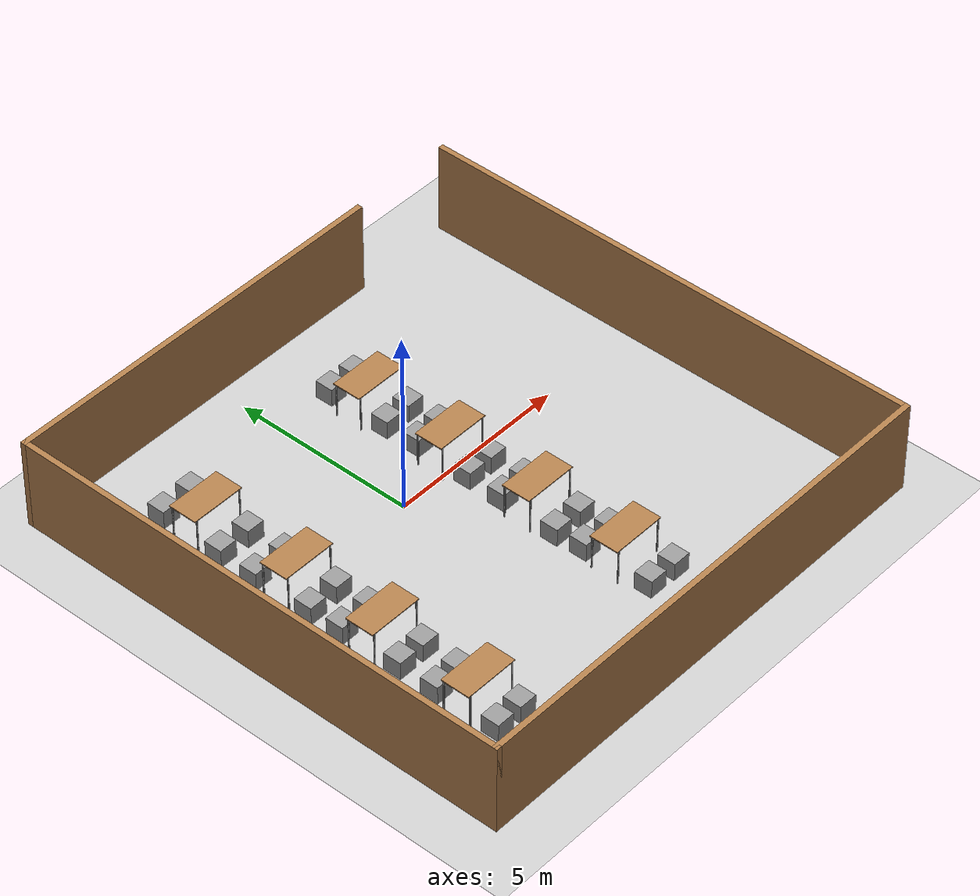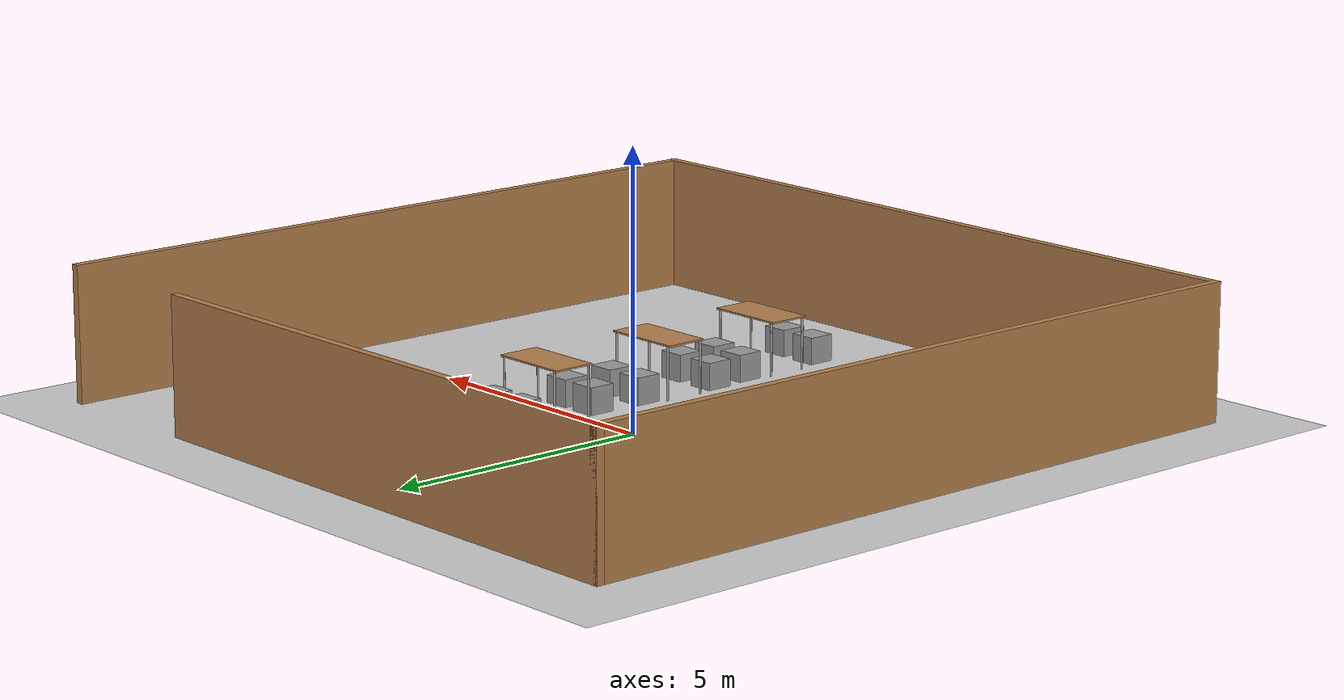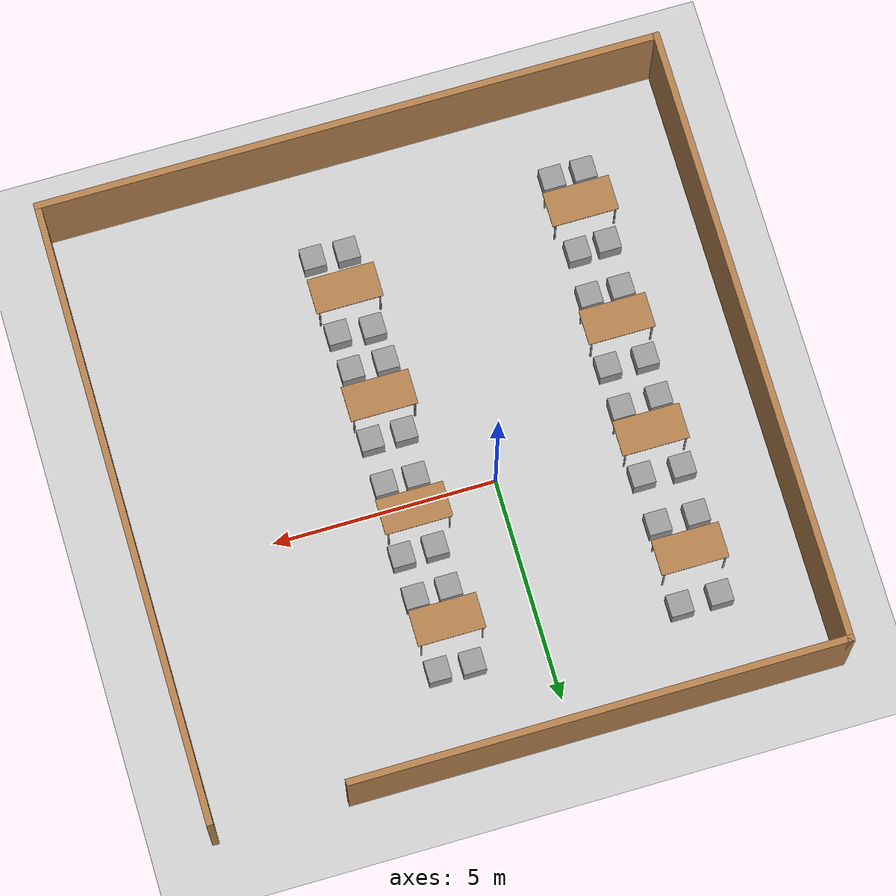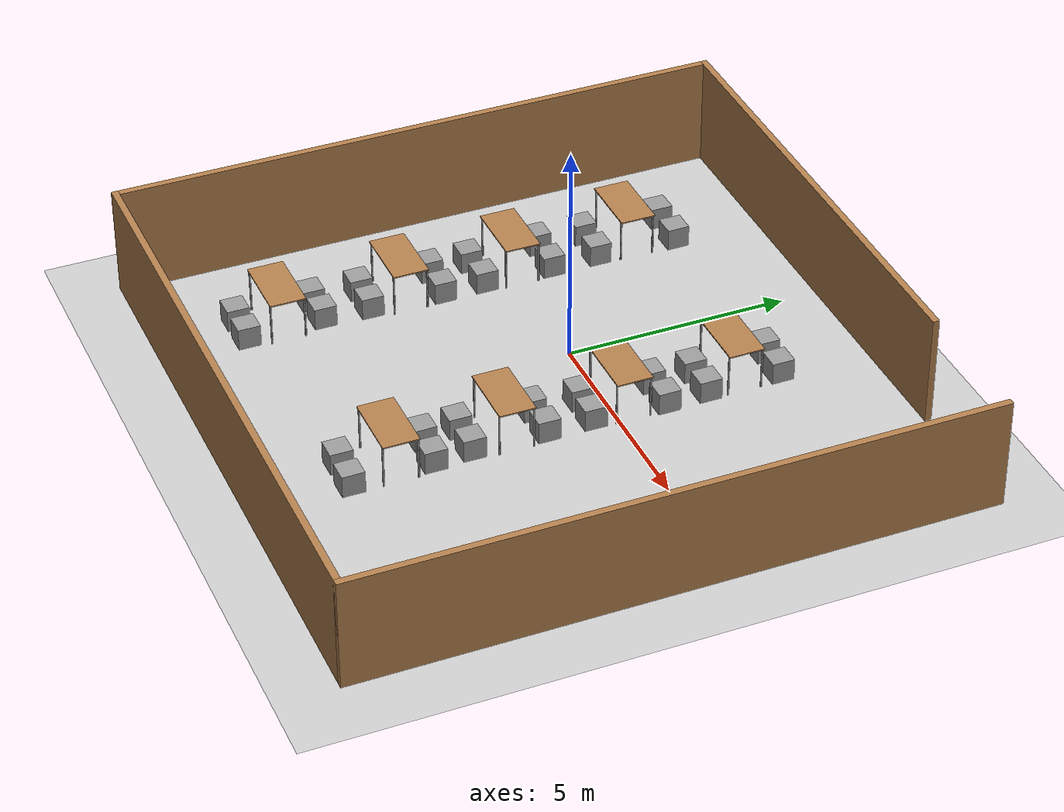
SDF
<sdf version="1.7">
 <world name="default">
  <light name="sun" type="directional">
   <pose>0 0 10 0 -0 0</pose>
   <diffuse>0.8 0.8 0.8 1</diffuse>
   <specular>0.2 0.2 0.2 1</specular>
   <attenuation>
    <range>1000</range>
    <constant>0.9</constant>
    <linear>0.01</linear>
    <quadratic>0.001</quadratic>
   </attenuation>
   <direction>-0.5 0.1 -0.9</direction>
   <spot><inner_angle>0</inner_angle><outer_angle>0</outer_angle><falloff>0</falloff></spot>
  </light>
  <model name="ground_plane">
   <static>1</static>
   <link name="link">
    <collision name="collision">
     <geometry><plane><normal>0 0 1</normal><size>100 100</size></plane></geometry>
     <surface><friction><ode><mu>100</mu><mu2>50</mu2></ode></friction></surface>
    </collision>
    <visual name="visual">
     <cast_shadows>0</cast_shadows>
     <geometry><plane><normal>0 0 1</normal><size>100 100</size></plane></geometry>
     <material>
      <script><uri>file://media/materials/scripts/gazebo.material</uri><name>Gazebo/Grey</name></script>
     </material>
    </visual>
   </link>
  </model>
  <gravity>0 0 -9.8</gravity>
  <magnetic_field>6e-06 2.3e-05 -4.2e-05</magnetic_field>
  <atmosphere type="adiabatic"/>
  <physics type="ode">
   <max_step_size>0.001</max_step_size>
   <real_time_factor>1</real_time_factor>
   <real_time_update_rate>1000</real_time_update_rate>
  </physics>
  <scene><ambient>0.4 0.4 0.4 1</ambient><background>0.7 0.7 0.7 1</background><shadows>1</shadows></scene>
  <audio><device>default</device></audio>
  <spherical_coordinates>
   <surface_model>EARTH_WGS84</surface_model>
   <latitude_deg>0</latitude_deg>
   <longitude_deg>0</longitude_deg>
   <elevation>0</elevation>
   <heading_deg>0</heading_deg>
  </spherical_coordinates>
  <model name="wall">
   <pose>0.983985 0.059169 0 0 -0 0</pose>
   <link name="Wall_20">
    <collision name="Wall_20_Collision">
     <geometry><box><size>11 0.15 2.5</size></box></geometry>
     <pose>0 0 1.25 0 -0 0</pose>
    </collision>
    <visual name="Wall_20_Visual">
     <pose>0 0 1.25 0 -0 0</pose>
     <geometry><box><size>11 0.15 2.5</size></box></geometry>
     <material>
      <script><uri>file://media/materials/scripts/gazebo.material</uri><name>Gazebo/Wood</name></script>
      <ambient>1 1 1 1</ambient>
     </material>
     <meta><layer>0</layer></meta>
    </visual>
    <pose>-1.5 5.81505 0 0 -0 0</pose>
   </link>
   <link name="Wall_22">
    <collision name="Wall_22_Collision">
     <geometry><box><size>14 0.15 2.5</size></box></geometry>
     <pose>0 0 1.25 0 -0 0</pose>
    </collision>
    <visual name="Wall_22_Visual">
     <pose>0 0 1.25 0 -0 0</pose>
     <geometry><box><size>14 0.15 2.5</size></box></geometry>
     <material>
      <script><uri>file://media/materials/scripts/gazebo.material</uri><name>Gazebo/Wood</name></script>
      <ambient>1 1 1 1</ambient>
     </material>
     <meta><layer>0</layer></meta>
    </visual>
    <pose>-6.925 -1.10995 0 0 -0 -1.5708</pose>
   </link>
   <link name="Wall_23">
    <collision name="Wall_23_Collision">
     <geometry><box><size>14 0.15 2.5</size></box></geometry>
     <pose>0 0 1.25 0 -0 0</pose>
    </collision>
    <visual name="Wall_23_Visual">
     <pose>0 0 1.25 0 -0 0</pose>
     <geometry><box><size>14 0.15 2.5</size></box></geometry>
     <material>
      <script><uri>file://media/materials/scripts/gazebo.material</uri><name>Gazebo/Wood</name></script>
      <ambient>1 1 1 1</ambient>
     </material>
     <meta><layer>0</layer></meta>
    </visual>
    <pose>-0 -8.03495 0 0 -0 0</pose>
   </link>
   <link name="Wall_24">
    <collision name="Wall_24_Collision">
     <geometry><box><size>14 0.15 2.5</size></box></geometry>
     <pose>0 0 1.25 0 -0 0</pose>
    </collision>
    <visual name="Wall_24_Visual">
     <pose>0 0 1.25 0 -0 0</pose>
     <geometry><box><size>14 0.15 2.5</size></box></geometry>
     <material>
      <script><uri>file://media/materials/scripts/gazebo.material</uri><name>Gazebo/Wood</name></script>
      <ambient>1 1 1 1</ambient>
     </material>
     <meta><layer>0</layer></meta>
    </visual>
    <pose>6.925 -1.10995 0 0 -0 1.5708</pose>
   </link>
   <static>1</static>
  </model>
  <model name="table">
   <static>1</static>
   <link name="link">
    <collision name="surface">
     <pose>0 0 1 0 -0 0</pose>
     <geometry><box><size>1.5 0.8 0.03</size></box></geometry>
     <surface><friction><ode><mu>0.6</mu><mu2>0.6</mu2></ode></friction></surface>
    </collision>
    <visual name="visual1">
     <pose>0 0 1 0 -0 0</pose>
     <geometry><box><size>1.5 0.8 0.03</size></box></geometry>
     <material>
      <script><uri>file://media/materials/scripts/gazebo.material</uri><name>Gazebo/Wood</name></script>
     </material>
    </visual>
    <collision name="front_left_leg">
     <pose>0.68 0.38 0.5 0 -0 0</pose>
     <geometry><cylinder><radius>0.02</radius><length>1</length></cylinder></geometry>
    </collision>
    <visual name="front_left_leg">
     <pose>0.68 0.38 0.5 0 -0 0</pose>
     <geometry><cylinder><radius>0.02</radius><length>1</length></cylinder></geometry>
     <material>
      <script><uri>file://media/materials/scripts/gazebo.material</uri><name>Gazebo/Grey</name></script>
     </material>
    </visual>
    <collision name="front_right_leg">
     <pose>0.68 -0.38 0.5 0 -0 0</pose>
     <geometry><cylinder><radius>0.02</radius><length>1</length></cylinder></geometry>
    </collision>
    <visual name="front_right_leg">
     <pose>0.68 -0.38 0.5 0 -0 0</pose>
     <geometry><cylinder><radius>0.02</radius><length>1</length></cylinder></geometry>
     <material>
      <script><uri>file://media/materials/scripts/gazebo.material</uri><name>Gazebo/Grey</name></script>
     </material>
    </visual>
    <collision name="back_right_leg">
     <pose>-0.68 -0.38 0.5 0 -0 0</pose>
     <geometry><cylinder><radius>0.02</radius><length>1</length></cylinder></geometry>
    </collision>
    <visual name="back_right_leg">
     <pose>-0.68 -0.38 0.5 0 -0 0</pose>
     <geometry><cylinder><radius>0.02</radius><length>1</length></cylinder></geometry>
     <material>
      <script><uri>file://media/materials/scripts/gazebo.material</uri><name>Gazebo/Grey</name></script>
     </material>
    </visual>
    <collision name="back_left_leg">
     <pose>-0.68 0.38 0.5 0 -0 0</pose>
     <geometry><cylinder><radius>0.02</radius><length>1</length></cylinder></geometry>
    </collision>
    <visual name="back_left_leg">
     <pose>-0.68 0.38 0.5 0 -0 0</pose>
     <geometry><cylinder><radius>0.02</radius><length>1</length></cylinder></geometry>
     <material>
      <script><uri>file://media/materials/scripts/gazebo.material</uri><name>Gazebo/Grey</name></script>
     </material>
    </visual>
   </link>
   <pose>-3.47502 2.80733 0 0 -0 0</pose>
  </model>
  <model name="table_0">
   <static>1</static>
   <link name="link">
    <collision name="surface">
     <pose>0 0 1 0 -0 0</pose>
     <geometry><box><size>1.5 0.8 0.03</size></box></geometry>
     <surface><friction><ode><mu>0.6</mu><mu2>0.6</mu2></ode></friction></surface>
    </collision>
    <visual name="visual1">
     <pose>0 0 1 0 -0 0</pose>
     <geometry><box><size>1.5 0.8 0.03</size></box></geometry>
     <material>
      <script><uri>file://media/materials/scripts/gazebo.material</uri><name>Gazebo/Wood</name></script>
     </material>
    </visual>
    <collision name="front_left_leg">
     <pose>0.68 0.38 0.5 0 -0 0</pose>
     <geometry><cylinder><radius>0.02</radius><length>1</length></cylinder></geometry>
    </collision>
    <visual name="front_left_leg">
     <pose>0.68 0.38 0.5 0 -0 0</pose>
     <geometry><cylinder><radius>0.02</radius><length>1</length></cylinder></geometry>
     <material>
      <script><uri>file://media/materials/scripts/gazebo.material</uri><name>Gazebo/Grey</name></script>
     </material>
    </visual>
    <collision name="front_right_leg">
     <pose>0.68 -0.38 0.5 0 -0 0</pose>
     <geometry><cylinder><radius>0.02</radius><length>1</length></cylinder></geometry>
    </collision>
    <visual name="front_right_leg">
     <pose>0.68 -0.38 0.5 0 -0 0</pose>
     <geometry><cylinder><radius>0.02</radius><length>1</length></cylinder></geometry>
     <material>
      <script><uri>file://media/materials/scripts/gazebo.material</uri><name>Gazebo/Grey</name></script>
     </material>
    </visual>
    <collision name="back_right_leg">
     <pose>-0.68 -0.38 0.5 0 -0 0</pose>
     <geometry><cylinder><radius>0.02</radius><length>1</length></cylinder></geometry>
    </collision>
    <visual name="back_right_leg">
     <pose>-0.68 -0.38 0.5 0 -0 0</pose>
     <geometry><cylinder><radius>0.02</radius><length>1</length></cylinder></geometry>
     <material>
      <script><uri>file://media/materials/scripts/gazebo.material</uri><name>Gazebo/Grey</name></script>
     </material>
    </visual>
    <collision name="back_left_leg">
     <pose>-0.68 0.38 0.5 0 -0 0</pose>
     <geometry><cylinder><radius>0.02</radius><length>1</length></cylinder></geometry>
    </collision>
    <visual name="back_left_leg">
     <pose>-0.68 0.38 0.5 0 -0 0</pose>
     <geometry><cylinder><radius>0.02</radius><length>1</length></cylinder></geometry>
     <material>
      <script><uri>file://media/materials/scripts/gazebo.material</uri><name>Gazebo/Grey</name></script>
     </material>
    </visual>
   </link>
   <pose>-3.43785 0.065077 0 0 -0 0</pose>
  </model>
  <model name="table_1">
   <static>1</static>
   <link name="link">
    <collision name="surface">
     <pose>0 0 1 0 -0 0</pose>
     <geometry><box><size>1.5 0.8 0.03</size></box></geometry>
     <surface><friction><ode><mu>0.6</mu><mu2>0.6</mu2></ode></friction></surface>
    </collision>
    <visual name="visual1">
     <pose>0 0 1 0 -0 0</pose>
     <geometry><box><size>1.5 0.8 0.03</size></box></geometry>
     <material>
      <script><uri>file://media/materials/scripts/gazebo.material</uri><name>Gazebo/Wood</name></script>
     </material>
    </visual>
    <collision name="front_left_leg">
     <pose>0.68 0.38 0.5 0 -0 0</pose>
     <geometry><cylinder><radius>0.02</radius><length>1</length></cylinder></geometry>
    </collision>
    <visual name="front_left_leg">
     <pose>0.68 0.38 0.5 0 -0 0</pose>
     <geometry><cylinder><radius>0.02</radius><length>1</length></cylinder></geometry>
     <material>
      <script><uri>file://media/materials/scripts/gazebo.material</uri><name>Gazebo/Grey</name></script>
     </material>
    </visual>
    <collision name="front_right_leg">
     <pose>0.68 -0.38 0.5 0 -0 0</pose>
     <geometry><cylinder><radius>0.02</radius><length>1</length></cylinder></geometry>
    </collision>
    <visual name="front_right_leg">
     <pose>0.68 -0.38 0.5 0 -0 0</pose>
     <geometry><cylinder><radius>0.02</radius><length>1</length></cylinder></geometry>
     <material>
      <script><uri>file://media/materials/scripts/gazebo.material</uri><name>Gazebo/Grey</name></script>
     </material>
    </visual>
    <collision name="back_right_leg">
     <pose>-0.68 -0.38 0.5 0 -0 0</pose>
     <geometry><cylinder><radius>0.02</radius><length>1</length></cylinder></geometry>
    </collision>
    <visual name="back_right_leg">
     <pose>-0.68 -0.38 0.5 0 -0 0</pose>
     <geometry><cylinder><radius>0.02</radius><length>1</length></cylinder></geometry>
     <material>
      <script><uri>file://media/materials/scripts/gazebo.material</uri><name>Gazebo/Grey</name></script>
     </material>
    </visual>
    <collision name="back_left_leg">
     <pose>-0.68 0.38 0.5 0 -0 0</pose>
     <geometry><cylinder><radius>0.02</radius><length>1</length></cylinder></geometry>
    </collision>
    <visual name="back_left_leg">
     <pose>-0.68 0.38 0.5 0 -0 0</pose>
     <geometry><cylinder><radius>0.02</radius><length>1</length></cylinder></geometry>
     <material>
      <script><uri>file://media/materials/scripts/gazebo.material</uri><name>Gazebo/Grey</name></script>
     </material>
    </visual>
   </link>
   <pose>-3.46014 -2.51399 0 0 -0 0</pose>
  </model>
  <model name="table_2">
   <static>1</static>
   <link name="link">
    <collision name="surface">
     <pose>0 0 1 0 -0 0</pose>
     <geometry><box><size>1.5 0.8 0.03</size></box></geometry>
     <surface><friction><ode><mu>0.6</mu><mu2>0.6</mu2></ode></friction></surface>
    </collision>
    <visual name="visual1">
     <pose>0 0 1 0 -0 0</pose>
     <geometry><box><size>1.5 0.8 0.03</size></box></geometry>
     <material>
      <script><uri>file://media/materials/scripts/gazebo.material</uri><name>Gazebo/Wood</name></script>
     </material>
    </visual>
    <collision name="front_left_leg">
     <pose>0.68 0.38 0.5 0 -0 0</pose>
     <geometry><cylinder><radius>0.02</radius><length>1</length></cylinder></geometry>
    </collision>
    <visual name="front_left_leg">
     <pose>0.68 0.38 0.5 0 -0 0</pose>
     <geometry><cylinder><radius>0.02</radius><length>1</length></cylinder></geometry>
     <material>
      <script><uri>file://media/materials/scripts/gazebo.material</uri><name>Gazebo/Grey</name></script>
     </material>
    </visual>
    <collision name="front_right_leg">
     <pose>0.68 -0.38 0.5 0 -0 0</pose>
     <geometry><cylinder><radius>0.02</radius><length>1</length></cylinder></geometry>
    </collision>
    <visual name="front_right_leg">
     <pose>0.68 -0.38 0.5 0 -0 0</pose>
     <geometry><cylinder><radius>0.02</radius><length>1</length></cylinder></geometry>
     <material>
      <script><uri>file://media/materials/scripts/gazebo.material</uri><name>Gazebo/Grey</name></script>
     </material>
    </visual>
    <collision name="back_right_leg">
     <pose>-0.68 -0.38 0.5 0 -0 0</pose>
     <geometry><cylinder><radius>0.02</radius><length>1</length></cylinder></geometry>
    </collision>
    <visual name="back_right_leg">
     <pose>-0.68 -0.38 0.5 0 -0 0</pose>
     <geometry><cylinder><radius>0.02</radius><length>1</length></cylinder></geometry>
     <material>
      <script><uri>file://media/materials/scripts/gazebo.material</uri><name>Gazebo/Grey</name></script>
     </material>
    </visual>
    <collision name="back_left_leg">
     <pose>-0.68 0.38 0.5 0 -0 0</pose>
     <geometry><cylinder><radius>0.02</radius><length>1</length></cylinder></geometry>
    </collision>
    <visual name="back_left_leg">
     <pose>-0.68 0.38 0.5 0 -0 0</pose>
     <geometry><cylinder><radius>0.02</radius><length>1</length></cylinder></geometry>
     <material>
      <script><uri>file://media/materials/scripts/gazebo.material</uri><name>Gazebo/Grey</name></script>
     </material>
    </visual>
   </link>
   <pose>-3.46984 -5.28766 0 0 -0 0</pose>
  </model>
  <model name="table_3">
   <static>1</static>
   <link name="link">
    <collision name="surface">
     <pose>0 0 1 0 -0 0</pose>
     <geometry><box><size>1.5 0.8 0.03</size></box></geometry>
     <surface><friction><ode><mu>0.6</mu><mu2>0.6</mu2></ode></friction></surface>
    </collision>
    <visual name="visual1">
     <pose>0 0 1 0 -0 0</pose>
     <geometry><box><size>1.5 0.8 0.03</size></box></geometry>
     <material>
      <script><uri>file://media/materials/scripts/gazebo.material</uri><name>Gazebo/Wood</name></script>
     </material>
    </visual>
    <collision name="front_left_leg">
     <pose>0.68 0.38 0.5 0 -0 0</pose>
     <geometry><cylinder><radius>0.02</radius><length>1</length></cylinder></geometry>
    </collision>
    <visual name="front_left_leg">
     <pose>0.68 0.38 0.5 0 -0 0</pose>
     <geometry><cylinder><radius>0.02</radius><length>1</length></cylinder></geometry>
     <material>
      <script><uri>file://media/materials/scripts/gazebo.material</uri><name>Gazebo/Grey</name></script>
     </material>
    </visual>
    <collision name="front_right_leg">
     <pose>0.68 -0.38 0.5 0 -0 0</pose>
     <geometry><cylinder><radius>0.02</radius><length>1</length></cylinder></geometry>
    </collision>
    <visual name="front_right_leg">
     <pose>0.68 -0.38 0.5 0 -0 0</pose>
     <geometry><cylinder><radius>0.02</radius><length>1</length></cylinder></geometry>
     <material>
      <script><uri>file://media/materials/scripts/gazebo.material</uri><name>Gazebo/Grey</name></script>
     </material>
    </visual>
    <collision name="back_right_leg">
     <pose>-0.68 -0.38 0.5 0 -0 0</pose>
     <geometry><cylinder><radius>0.02</radius><length>1</length></cylinder></geometry>
    </collision>
    <visual name="back_right_leg">
     <pose>-0.68 -0.38 0.5 0 -0 0</pose>
     <geometry><cylinder><radius>0.02</radius><length>1</length></cylinder></geometry>
     <material>
      <script><uri>file://media/materials/scripts/gazebo.material</uri><name>Gazebo/Grey</name></script>
     </material>
    </visual>
    <collision name="back_left_leg">
     <pose>-0.68 0.38 0.5 0 -0 0</pose>
     <geometry><cylinder><radius>0.02</radius><length>1</length></cylinder></geometry>
    </collision>
    <visual name="back_left_leg">
     <pose>-0.68 0.38 0.5 0 -0 0</pose>
     <geometry><cylinder><radius>0.02</radius><length>1</length></cylinder></geometry>
     <material>
      <script><uri>file://media/materials/scripts/gazebo.material</uri><name>Gazebo/Grey</name></script>
     </material>
    </visual>
   </link>
   <pose>1.92457 2.83936 0 0 -0 0</pose>
  </model>
  <model name="table_4">
   <static>1</static>
   <link name="link">
    <collision name="surface">
     <pose>0 0 1 0 -0 0</pose>
     <geometry><box><size>1.5 0.8 0.03</size></box></geometry>
     <surface><friction><ode><mu>0.6</mu><mu2>0.6</mu2></ode></friction></surface>
    </collision>
    <visual name="visual1">
     <pose>0 0 1 0 -0 0</pose>
     <geometry><box><size>1.5 0.8 0.03</size></box></geometry>
     <material>
      <script><uri>file://media/materials/scripts/gazebo.material</uri><name>Gazebo/Wood</name></script>
     </material>
    </visual>
    <collision name="front_left_leg">
     <pose>0.68 0.38 0.5 0 -0 0</pose>
     <geometry><cylinder><radius>0.02</radius><length>1</length></cylinder></geometry>
    </collision>
    <visual name="front_left_leg">
     <pose>0.68 0.38 0.5 0 -0 0</pose>
     <geometry><cylinder><radius>0.02</radius><length>1</length></cylinder></geometry>
     <material>
      <script><uri>file://media/materials/scripts/gazebo.material</uri><name>Gazebo/Grey</name></script>
     </material>
    </visual>
    <collision name="front_right_leg">
     <pose>0.68 -0.38 0.5 0 -0 0</pose>
     <geometry><cylinder><radius>0.02</radius><length>1</length></cylinder></geometry>
    </collision>
    <visual name="front_right_leg">
     <pose>0.68 -0.38 0.5 0 -0 0</pose>
     <geometry><cylinder><radius>0.02</radius><length>1</length></cylinder></geometry>
     <material>
      <script><uri>file://media/materials/scripts/gazebo.material</uri><name>Gazebo/Grey</name></script>
     </material>
    </visual>
    <collision name="back_right_leg">
     <pose>-0.68 -0.38 0.5 0 -0 0</pose>
     <geometry><cylinder><radius>0.02</radius><length>1</length></cylinder></geometry>
    </collision>
    <visual name="back_right_leg">
     <pose>-0.68 -0.38 0.5 0 -0 0</pose>
     <geometry><cylinder><radius>0.02</radius><length>1</length></cylinder></geometry>
     <material>
      <script><uri>file://media/materials/scripts/gazebo.material</uri><name>Gazebo/Grey</name></script>
     </material>
    </visual>
    <collision name="back_left_leg">
     <pose>-0.68 0.38 0.5 0 -0 0</pose>
     <geometry><cylinder><radius>0.02</radius><length>1</length></cylinder></geometry>
    </collision>
    <visual name="back_left_leg">
     <pose>-0.68 0.38 0.5 0 -0 0</pose>
     <geometry><cylinder><radius>0.02</radius><length>1</length></cylinder></geometry>
     <material>
      <script><uri>file://media/materials/scripts/gazebo.material</uri><name>Gazebo/Grey</name></script>
     </material>
    </visual>
   </link>
   <pose>1.92033 0.311512 0 0 -0 0</pose>
  </model>
  <model name="table_5">
   <static>1</static>
   <link name="link">
    <collision name="surface">
     <pose>0 0 1 0 -0 0</pose>
     <geometry><box><size>1.5 0.8 0.03</size></box></geometry>
     <surface><friction><ode><mu>0.6</mu><mu2>0.6</mu2></ode></friction></surface>
    </collision>
    <visual name="visual1">
     <pose>0 0 1 0 -0 0</pose>
     <geometry><box><size>1.5 0.8 0.03</size></box></geometry>
     <material>
      <script><uri>file://media/materials/scripts/gazebo.material</uri><name>Gazebo/Wood</name></script>
     </material>
    </visual>
    <collision name="front_left_leg">
     <pose>0.68 0.38 0.5 0 -0 0</pose>
     <geometry><cylinder><radius>0.02</radius><length>1</length></cylinder></geometry>
    </collision>
    <visual name="front_left_leg">
     <pose>0.68 0.38 0.5 0 -0 0</pose>
     <geometry><cylinder><radius>0.02</radius><length>1</length></cylinder></geometry>
     <material>
      <script><uri>file://media/materials/scripts/gazebo.material</uri><name>Gazebo/Grey</name></script>
     </material>
    </visual>
    <collision name="front_right_leg">
     <pose>0.68 -0.38 0.5 0 -0 0</pose>
     <geometry><cylinder><radius>0.02</radius><length>1</length></cylinder></geometry>
    </collision>
    <visual name="front_right_leg">
     <pose>0.68 -0.38 0.5 0 -0 0</pose>
     <geometry><cylinder><radius>0.02</radius><length>1</length></cylinder></geometry>
     <material>
      <script><uri>file://media/materials/scripts/gazebo.material</uri><name>Gazebo/Grey</name></script>
     </material>
    </visual>
    <collision name="back_right_leg">
     <pose>-0.68 -0.38 0.5 0 -0 0</pose>
     <geometry><cylinder><radius>0.02</radius><length>1</length></cylinder></geometry>
    </collision>
    <visual name="back_right_leg">
     <pose>-0.68 -0.38 0.5 0 -0 0</pose>
     <geometry><cylinder><radius>0.02</radius><length>1</length></cylinder></geometry>
     <material>
      <script><uri>file://media/materials/scripts/gazebo.material</uri><name>Gazebo/Grey</name></script>
     </material>
    </visual>
    <collision name="back_left_leg">
     <pose>-0.68 0.38 0.5 0 -0 0</pose>
     <geometry><cylinder><radius>0.02</radius><length>1</length></cylinder></geometry>
    </collision>
    <visual name="back_left_leg">
     <pose>-0.68 0.38 0.5 0 -0 0</pose>
     <geometry><cylinder><radius>0.02</radius><length>1</length></cylinder></geometry>
     <material>
      <script><uri>file://media/materials/scripts/gazebo.material</uri><name>Gazebo/Grey</name></script>
     </material>
    </visual>
   </link>
   <pose>1.94221 -2.29258 0 0 -0 0</pose>
  </model>
  <model name="table_6">
   <static>1</static>
   <link name="link">
    <collision name="surface">
     <pose>0 0 1 0 -0 0</pose>
     <geometry><box><size>1.5 0.8 0.03</size></box></geometry>
     <surface><friction><ode><mu>0.6</mu><mu2>0.6</mu2></ode></friction></surface>
    </collision>
    <visual name="visual1">
     <pose>0 0 1 0 -0 0</pose>
     <geometry><box><size>1.5 0.8 0.03</size></box></geometry>
     <material>
      <script><uri>file://media/materials/scripts/gazebo.material</uri><name>Gazebo/Wood</name></script>
     </material>
    </visual>
    <collision name="front_left_leg">
     <pose>0.68 0.38 0.5 0 -0 0</pose>
     <geometry><cylinder><radius>0.02</radius><length>1</length></cylinder></geometry>
    </collision>
    <visual name="front_left_leg">
     <pose>0.68 0.38 0.5 0 -0 0</pose>
     <geometry><cylinder><radius>0.02</radius><length>1</length></cylinder></geometry>
     <material>
      <script><uri>file://media/materials/scripts/gazebo.material</uri><name>Gazebo/Grey</name></script>
     </material>
    </visual>
    <collision name="front_right_leg">
     <pose>0.68 -0.38 0.5 0 -0 0</pose>
     <geometry><cylinder><radius>0.02</radius><length>1</length></cylinder></geometry>
    </collision>
    <visual name="front_right_leg">
     <pose>0.68 -0.38 0.5 0 -0 0</pose>
     <geometry><cylinder><radius>0.02</radius><length>1</length></cylinder></geometry>
     <material>
      <script><uri>file://media/materials/scripts/gazebo.material</uri><name>Gazebo/Grey</name></script>
     </material>
    </visual>
    <collision name="back_right_leg">
     <pose>-0.68 -0.38 0.5 0 -0 0</pose>
     <geometry><cylinder><radius>0.02</radius><length>1</length></cylinder></geometry>
    </collision>
    <visual name="back_right_leg">
     <pose>-0.68 -0.38 0.5 0 -0 0</pose>
     <geometry><cylinder><radius>0.02</radius><length>1</length></cylinder></geometry>
     <material>
      <script><uri>file://media/materials/scripts/gazebo.material</uri><name>Gazebo/Grey</name></script>
     </material>
    </visual>
    <collision name="back_left_leg">
     <pose>-0.68 0.38 0.5 0 -0 0</pose>
     <geometry><cylinder><radius>0.02</radius><length>1</length></cylinder></geometry>
    </collision>
    <visual name="back_left_leg">
     <pose>-0.68 0.38 0.5 0 -0 0</pose>
     <geometry><cylinder><radius>0.02</radius><length>1</length></cylinder></geometry>
     <material>
      <script><uri>file://media/materials/scripts/gazebo.material</uri><name>Gazebo/Grey</name></script>
     </material>
    </visual>
   </link>
   <pose>1.99333 -4.81792 0 0 -0 0</pose>
  </model>
  <model name="chair">
   <link name="link">
    <inertial>
     <mass>1</mass>
     <inertia>
      <ixx>0.166667</ixx>
      <ixy>0</ixy>
      <ixz>0</ixz>
      <iyy>0.166667</iyy>
      <iyz>0</iyz>
      <izz>0.166667</izz>
     </inertia>
    </inertial>
    <visual name="visual">
     <geometry><box><size>0.5 0.5 0.5</size></box></geometry>
     <material>
      <script><name>Gazebo/Grey</name><uri>file://media/materials/scripts/gazebo.material</uri></script>
      <shader type="pixel"><normal_map>__default__</normal_map></shader>
      <ambient>0.3 0.3 0.3 1</ambient>
      <diffuse>0.7 0.7 0.7 1</diffuse>
      <specular>0.01 0.01 0.01 1</specular>
      <emissive>0 0 0 1</emissive>
     </material>
    </visual>
    <collision name="collision">
     <geometry><box><size>0.5 0.5 0.5</size></box></geometry>
     <surface>
      <friction>
       <ode><mu>1</mu><mu2>1</mu2><fdir1>0 0 0</fdir1><slip1>0</slip1><slip2>0</slip2></ode>
       <torsional>
        <coefficient>1</coefficient>
        <patch_radius>0</patch_radius>
        <surface_radius>0</surface_radius>
        <use_patch_radius>1</use_patch_radius>
        <ode><slip>0</slip></ode>
       </torsional>
      </friction>
      <bounce><restitution_coefficient>0</restitution_coefficient><threshold>1e+06</threshold></bounce>
      <contact>
       <collide_without_contact>0</collide_without_contact>
       <collide_without_contact_bitmask>1</collide_without_contact_bitmask>
       <collide_bitmask>1</collide_bitmask>
       <ode>
        <soft_cfm>0</soft_cfm>
        <soft_erp>0.2</soft_erp>
        <kp>1e+13</kp>
        <kd>1</kd>
        <max_vel>0.01</max_vel>
        <min_depth>0</min_depth>
       </ode>
       <bullet>
        <split_impulse>1</split_impulse>
        <split_impulse_penetration_threshold>-0.01</split_impulse_penetration_threshold>
        <soft_cfm>0</soft_cfm>
        <soft_erp>0.2</soft_erp>
        <kp>1e+13</kp>
        <kd>1</kd>
       </bullet>
      </contact>
     </surface>
    </collision>
   </link>
   <static>0</static>
   <pose>-3.86503 3.7887 0.25 0 -0 0</pose>
  </model>
  <model name="chair_0">
   <link name="link">
    <inertial>
     <mass>1</mass>
     <inertia>
      <ixx>0.166667</ixx>
      <ixy>0</ixy>
      <ixz>0</ixz>
      <iyy>0.166667</iyy>
      <iyz>0</iyz>
      <izz>0.166667</izz>
     </inertia>
    </inertial>
    <visual name="visual">
     <geometry><box><size>0.5 0.5 0.5</size></box></geometry>
     <material>
      <script><name>Gazebo/Grey</name><uri>file://media/materials/scripts/gazebo.material</uri></script>
      <shader type="pixel"><normal_map>__default__</normal_map></shader>
      <ambient>0.3 0.3 0.3 1</ambient>
      <diffuse>0.7 0.7 0.7 1</diffuse>
      <specular>0.01 0.01 0.01 1</specular>
      <emissive>0 0 0 1</emissive>
     </material>
    </visual>
    <collision name="collision">
     <geometry><box><size>0.5 0.5 0.5</size></box></geometry>
     <surface>
      <friction>
       <ode><mu>1</mu><mu2>1</mu2><fdir1>0 0 0</fdir1><slip1>0</slip1><slip2>0</slip2></ode>
       <torsional>
        <coefficient>1</coefficient>
        <patch_radius>0</patch_radius>
        <surface_radius>0</surface_radius>
        <use_patch_radius>1</use_patch_radius>
        <ode><slip>0</slip></ode>
       </torsional>
      </friction>
      <bounce><restitution_coefficient>0</restitution_coefficient><threshold>1e+06</threshold></bounce>
      <contact>
       <collide_without_contact>0</collide_without_contact>
       <collide_without_contact_bitmask>1</collide_without_contact_bitmask>
       <collide_bitmask>1</collide_bitmask>
       <ode>
        <soft_cfm>0</soft_cfm>
        <soft_erp>0.2</soft_erp>
        <kp>1e+13</kp>
        <kd>1</kd>
        <max_vel>0.01</max_vel>
        <min_depth>0</min_depth>
       </ode>
       <bullet>
        <split_impulse>1</split_impulse>
        <split_impulse_penetration_threshold>-0.01</split_impulse_penetration_threshold>
        <soft_cfm>0</soft_cfm>
        <soft_erp>0.2</soft_erp>
        <kp>1e+13</kp>
        <kd>1</kd>
       </bullet>
      </contact>
     </surface>
    </collision>
   </link>
   <static>0</static>
   <pose>-2.97801 3.78938 0.25 0 -0 0</pose>
  </model>
  <model name="chair_1">
   <link name="link">
    <inertial>
     <mass>1</mass>
     <inertia>
      <ixx>0.166667</ixx>
      <ixy>0</ixy>
      <ixz>0</ixz>
      <iyy>0.166667</iyy>
      <iyz>0</iyz>
      <izz>0.166667</izz>
     </inertia>
    </inertial>
    <visual name="visual">
     <geometry><box><size>0.5 0.5 0.5</size></box></geometry>
     <material>
      <script><name>Gazebo/Grey</name><uri>file://media/materials/scripts/gazebo.material</uri></script>
      <shader type="pixel"><normal_map>__default__</normal_map></shader>
      <ambient>0.3 0.3 0.3 1</ambient>
      <diffuse>0.7 0.7 0.7 1</diffuse>
      <specular>0.01 0.01 0.01 1</specular>
      <emissive>0 0 0 1</emissive>
     </material>
    </visual>
    <collision name="collision">
     <geometry><box><size>0.5 0.5 0.5</size></box></geometry>
     <surface>
      <friction>
       <ode><mu>1</mu><mu2>1</mu2><fdir1>0 0 0</fdir1><slip1>0</slip1><slip2>0</slip2></ode>
       <torsional>
        <coefficient>1</coefficient>
        <patch_radius>0</patch_radius>
        <surface_radius>0</surface_radius>
        <use_patch_radius>1</use_patch_radius>
        <ode><slip>0</slip></ode>
       </torsional>
      </friction>
      <bounce><restitution_coefficient>0</restitution_coefficient><threshold>1e+06</threshold></bounce>
      <contact>
       <collide_without_contact>0</collide_without_contact>
       <collide_without_contact_bitmask>1</collide_without_contact_bitmask>
       <collide_bitmask>1</collide_bitmask>
       <ode>
        <soft_cfm>0</soft_cfm>
        <soft_erp>0.2</soft_erp>
        <kp>1e+13</kp>
        <kd>1</kd>
        <max_vel>0.01</max_vel>
        <min_depth>0</min_depth>
       </ode>
       <bullet>
        <split_impulse>1</split_impulse>
        <split_impulse_penetration_threshold>-0.01</split_impulse_penetration_threshold>
        <soft_cfm>0</soft_cfm>
        <soft_erp>0.2</soft_erp>
        <kp>1e+13</kp>
        <kd>1</kd>
       </bullet>
      </contact>
     </surface>
    </collision>
   </link>
   <static>0</static>
   <pose>-3.90663 1.96762 0.25 0 -0 0</pose>
  </model>
  <model name="chair_2">
   <link name="link">
    <inertial>
     <mass>1</mass>
     <inertia>
      <ixx>0.166667</ixx>
      <ixy>0</ixy>
      <ixz>0</ixz>
      <iyy>0.166667</iyy>
      <iyz>0</iyz>
      <izz>0.166667</izz>
     </inertia>
    </inertial>
    <visual name="visual">
     <geometry><box><size>0.5 0.5 0.5</size></box></geometry>
     <material>
      <script><name>Gazebo/Grey</name><uri>file://media/materials/scripts/gazebo.material</uri></script>
      <shader type="pixel"><normal_map>__default__</normal_map></shader>
      <ambient>0.3 0.3 0.3 1</ambient>
      <diffuse>0.7 0.7 0.7 1</diffuse>
      <specular>0.01 0.01 0.01 1</specular>
      <emissive>0 0 0 1</emissive>
     </material>
    </visual>
    <collision name="collision">
     <geometry><box><size>0.5 0.5 0.5</size></box></geometry>
     <surface>
      <friction>
       <ode><mu>1</mu><mu2>1</mu2><fdir1>0 0 0</fdir1><slip1>0</slip1><slip2>0</slip2></ode>
       <torsional>
        <coefficient>1</coefficient>
        <patch_radius>0</patch_radius>
        <surface_radius>0</surface_radius>
        <use_patch_radius>1</use_patch_radius>
        <ode><slip>0</slip></ode>
       </torsional>
      </friction>
      <bounce><restitution_coefficient>0</restitution_coefficient><threshold>1e+06</threshold></bounce>
      <contact>
       <collide_without_contact>0</collide_without_contact>
       <collide_without_contact_bitmask>1</collide_without_contact_bitmask>
       <collide_bitmask>1</collide_bitmask>
       <ode>
        <soft_cfm>0</soft_cfm>
        <soft_erp>0.2</soft_erp>
        <kp>1e+13</kp>
        <kd>1</kd>
        <max_vel>0.01</max_vel>
        <min_depth>0</min_depth>
       </ode>
       <bullet>
        <split_impulse>1</split_impulse>
        <split_impulse_penetration_threshold>-0.01</split_impulse_penetration_threshold>
        <soft_cfm>0</soft_cfm>
        <soft_erp>0.2</soft_erp>
        <kp>1e+13</kp>
        <kd>1</kd>
       </bullet>
      </contact>
     </surface>
    </collision>
   </link>
   <static>0</static>
   <pose>-3.04817 1.94765 0.25 0 -0 0</pose>
  </model>
  <model name="chair_3">
   <link name="link">
    <inertial>
     <mass>1</mass>
     <inertia>
      <ixx>0.166667</ixx>
      <ixy>0</ixy>
      <ixz>0</ixz>
      <iyy>0.166667</iyy>
      <iyz>0</iyz>
      <izz>0.166667</izz>
     </inertia>
    </inertial>
    <visual name="visual">
     <geometry><box><size>0.5 0.5 0.5</size></box></geometry>
     <material>
      <script><name>Gazebo/Grey</name><uri>file://media/materials/scripts/gazebo.material</uri></script>
      <shader type="pixel"><normal_map>__default__</normal_map></shader>
      <ambient>0.3 0.3 0.3 1</ambient>
      <diffuse>0.7 0.7 0.7 1</diffuse>
      <specular>0.01 0.01 0.01 1</specular>
      <emissive>0 0 0 1</emissive>
     </material>
    </visual>
    <collision name="collision">
     <geometry><box><size>0.5 0.5 0.5</size></box></geometry>
     <surface>
      <friction>
       <ode><mu>1</mu><mu2>1</mu2><fdir1>0 0 0</fdir1><slip1>0</slip1><slip2>0</slip2></ode>
       <torsional>
        <coefficient>1</coefficient>
        <patch_radius>0</patch_radius>
        <surface_radius>0</surface_radius>
        <use_patch_radius>1</use_patch_radius>
        <ode><slip>0</slip></ode>
       </torsional>
      </friction>
      <bounce><restitution_coefficient>0</restitution_coefficient><threshold>1e+06</threshold></bounce>
      <contact>
       <collide_without_contact>0</collide_without_contact>
       <collide_without_contact_bitmask>1</collide_without_contact_bitmask>
       <collide_bitmask>1</collide_bitmask>
       <ode>
        <soft_cfm>0</soft_cfm>
        <soft_erp>0.2</soft_erp>
        <kp>1e+13</kp>
        <kd>1</kd>
        <max_vel>0.01</max_vel>
        <min_depth>0</min_depth>
       </ode>
       <bullet>
        <split_impulse>1</split_impulse>
        <split_impulse_penetration_threshold>-0.01</split_impulse_penetration_threshold>
        <soft_cfm>0</soft_cfm>
        <soft_erp>0.2</soft_erp>
        <kp>1e+13</kp>
        <kd>1</kd>
       </bullet>
      </contact>
     </surface>
    </collision>
   </link>
   <static>0</static>
   <pose>-3.89509 -0.756773 0.25 0 -0 0</pose>
  </model>
  <model name="chair_4">
   <link name="link">
    <inertial>
     <mass>1</mass>
     <inertia>
      <ixx>0.166667</ixx>
      <ixy>0</ixy>
      <ixz>0</ixz>
      <iyy>0.166667</iyy>
      <iyz>0</iyz>
      <izz>0.166667</izz>
     </inertia>
    </inertial>
    <visual name="visual">
     <geometry><box><size>0.5 0.5 0.5</size></box></geometry>
     <material>
      <script><name>Gazebo/Grey</name><uri>file://media/materials/scripts/gazebo.material</uri></script>
      <shader type="pixel"><normal_map>__default__</normal_map></shader>
      <ambient>0.3 0.3 0.3 1</ambient>
      <diffuse>0.7 0.7 0.7 1</diffuse>
      <specular>0.01 0.01 0.01 1</specular>
      <emissive>0 0 0 1</emissive>
     </material>
    </visual>
    <collision name="collision">
     <geometry><box><size>0.5 0.5 0.5</size></box></geometry>
     <surface>
      <friction>
       <ode><mu>1</mu><mu2>1</mu2><fdir1>0 0 0</fdir1><slip1>0</slip1><slip2>0</slip2></ode>
       <torsional>
        <coefficient>1</coefficient>
        <patch_radius>0</patch_radius>
        <surface_radius>0</surface_radius>
        <use_patch_radius>1</use_patch_radius>
        <ode><slip>0</slip></ode>
       </torsional>
      </friction>
      <bounce><restitution_coefficient>0</restitution_coefficient><threshold>1e+06</threshold></bounce>
      <contact>
       <collide_without_contact>0</collide_without_contact>
       <collide_without_contact_bitmask>1</collide_without_contact_bitmask>
       <collide_bitmask>1</collide_bitmask>
       <ode>
        <soft_cfm>0</soft_cfm>
        <soft_erp>0.2</soft_erp>
        <kp>1e+13</kp>
        <kd>1</kd>
        <max_vel>0.01</max_vel>
        <min_depth>0</min_depth>
       </ode>
       <bullet>
        <split_impulse>1</split_impulse>
        <split_impulse_penetration_threshold>-0.01</split_impulse_penetration_threshold>
        <soft_cfm>0</soft_cfm>
        <soft_erp>0.2</soft_erp>
        <kp>1e+13</kp>
        <kd>1</kd>
       </bullet>
      </contact>
     </surface>
    </collision>
   </link>
   <static>0</static>
   <pose>-3.04257 -0.73259 0.25 0 -0 0</pose>
  </model>
  <model name="chair_5">
   <link name="link">
    <inertial>
     <mass>1</mass>
     <inertia>
      <ixx>0.166667</ixx>
      <ixy>0</ixy>
      <ixz>0</ixz>
      <iyy>0.166667</iyy>
      <iyz>0</iyz>
      <izz>0.166667</izz>
     </inertia>
    </inertial>
    <visual name="visual">
     <geometry><box><size>0.5 0.5 0.5</size></box></geometry>
     <material>
      <script><name>Gazebo/Grey</name><uri>file://media/materials/scripts/gazebo.material</uri></script>
      <shader type="pixel"><normal_map>__default__</normal_map></shader>
      <ambient>0.3 0.3 0.3 1</ambient>
      <diffuse>0.7 0.7 0.7 1</diffuse>
      <specular>0.01 0.01 0.01 1</specular>
      <emissive>0 0 0 1</emissive>
     </material>
    </visual>
    <collision name="collision">
     <geometry><box><size>0.5 0.5 0.5</size></box></geometry>
     <surface>
      <friction>
       <ode><mu>1</mu><mu2>1</mu2><fdir1>0 0 0</fdir1><slip1>0</slip1><slip2>0</slip2></ode>
       <torsional>
        <coefficient>1</coefficient>
        <patch_radius>0</patch_radius>
        <surface_radius>0</surface_radius>
        <use_patch_radius>1</use_patch_radius>
        <ode><slip>0</slip></ode>
       </torsional>
      </friction>
      <bounce><restitution_coefficient>0</restitution_coefficient><threshold>1e+06</threshold></bounce>
      <contact>
       <collide_without_contact>0</collide_without_contact>
       <collide_without_contact_bitmask>1</collide_without_contact_bitmask>
       <collide_bitmask>1</collide_bitmask>
       <ode>
        <soft_cfm>0</soft_cfm>
        <soft_erp>0.2</soft_erp>
        <kp>1e+13</kp>
        <kd>1</kd>
        <max_vel>0.01</max_vel>
        <min_depth>0</min_depth>
       </ode>
       <bullet>
        <split_impulse>1</split_impulse>
        <split_impulse_penetration_threshold>-0.01</split_impulse_penetration_threshold>
        <soft_cfm>0</soft_cfm>
        <soft_erp>0.2</soft_erp>
        <kp>1e+13</kp>
        <kd>1</kd>
       </bullet>
      </contact>
     </surface>
    </collision>
   </link>
   <static>0</static>
   <pose>-3.92308 0.880823 0.25 0 -0 0</pose>
  </model>
  <model name="chair_6">
   <link name="link">
    <inertial>
     <mass>1</mass>
     <inertia>
      <ixx>0.166667</ixx>
      <ixy>0</ixy>
      <ixz>0</ixz>
      <iyy>0.166667</iyy>
      <iyz>0</iyz>
      <izz>0.166667</izz>
     </inertia>
    </inertial>
    <visual name="visual">
     <geometry><box><size>0.5 0.5 0.5</size></box></geometry>
     <material>
      <script><name>Gazebo/Grey</name><uri>file://media/materials/scripts/gazebo.material</uri></script>
      <shader type="pixel"><normal_map>__default__</normal_map></shader>
      <ambient>0.3 0.3 0.3 1</ambient>
      <diffuse>0.7 0.7 0.7 1</diffuse>
      <specular>0.01 0.01 0.01 1</specular>
      <emissive>0 0 0 1</emissive>
     </material>
    </visual>
    <collision name="collision">
     <geometry><box><size>0.5 0.5 0.5</size></box></geometry>
     <surface>
      <friction>
       <ode><mu>1</mu><mu2>1</mu2><fdir1>0 0 0</fdir1><slip1>0</slip1><slip2>0</slip2></ode>
       <torsional>
        <coefficient>1</coefficient>
        <patch_radius>0</patch_radius>
        <surface_radius>0</surface_radius>
        <use_patch_radius>1</use_patch_radius>
        <ode><slip>0</slip></ode>
       </torsional>
      </friction>
      <bounce><restitution_coefficient>0</restitution_coefficient><threshold>1e+06</threshold></bounce>
      <contact>
       <collide_without_contact>0</collide_without_contact>
       <collide_without_contact_bitmask>1</collide_without_contact_bitmask>
       <collide_bitmask>1</collide_bitmask>
       <ode>
        <soft_cfm>0</soft_cfm>
        <soft_erp>0.2</soft_erp>
        <kp>1e+13</kp>
        <kd>1</kd>
        <max_vel>0.01</max_vel>
        <min_depth>0</min_depth>
       </ode>
       <bullet>
        <split_impulse>1</split_impulse>
        <split_impulse_penetration_threshold>-0.01</split_impulse_penetration_threshold>
        <soft_cfm>0</soft_cfm>
        <soft_erp>0.2</soft_erp>
        <kp>1e+13</kp>
        <kd>1</kd>
       </bullet>
      </contact>
     </surface>
    </collision>
   </link>
   <static>0</static>
   <pose>-3.02496 0.836207 0.25 0 -0 0</pose>
  </model>
  <model name="chair_7">
   <link name="link">
    <inertial>
     <mass>1</mass>
     <inertia>
      <ixx>0.166667</ixx>
      <ixy>0</ixy>
      <ixz>0</ixz>
      <iyy>0.166667</iyy>
      <iyz>0</iyz>
      <izz>0.166667</izz>
     </inertia>
    </inertial>
    <visual name="visual">
     <geometry><box><size>0.5 0.5 0.5</size></box></geometry>
     <material>
      <script><name>Gazebo/Grey</name><uri>file://media/materials/scripts/gazebo.material</uri></script>
      <shader type="pixel"><normal_map>__default__</normal_map></shader>
      <ambient>0.3 0.3 0.3 1</ambient>
      <diffuse>0.7 0.7 0.7 1</diffuse>
      <specular>0.01 0.01 0.01 1</specular>
      <emissive>0 0 0 1</emissive>
     </material>
    </visual>
    <collision name="collision">
     <geometry><box><size>0.5 0.5 0.5</size></box></geometry>
     <surface>
      <friction>
       <ode><mu>1</mu><mu2>1</mu2><fdir1>0 0 0</fdir1><slip1>0</slip1><slip2>0</slip2></ode>
       <torsional>
        <coefficient>1</coefficient>
        <patch_radius>0</patch_radius>
        <surface_radius>0</surface_radius>
        <use_patch_radius>1</use_patch_radius>
        <ode><slip>0</slip></ode>
       </torsional>
      </friction>
      <bounce><restitution_coefficient>0</restitution_coefficient><threshold>1e+06</threshold></bounce>
      <contact>
       <collide_without_contact>0</collide_without_contact>
       <collide_without_contact_bitmask>1</collide_without_contact_bitmask>
       <collide_bitmask>1</collide_bitmask>
       <ode>
        <soft_cfm>0</soft_cfm>
        <soft_erp>0.2</soft_erp>
        <kp>1e+13</kp>
        <kd>1</kd>
        <max_vel>0.01</max_vel>
        <min_depth>0</min_depth>
       </ode>
       <bullet>
        <split_impulse>1</split_impulse>
        <split_impulse_penetration_threshold>-0.01</split_impulse_penetration_threshold>
        <soft_cfm>0</soft_cfm>
        <soft_erp>0.2</soft_erp>
        <kp>1e+13</kp>
        <kd>1</kd>
       </bullet>
      </contact>
     </surface>
    </collision>
   </link>
   <static>0</static>
   <pose>-3.87613 -1.6864 0.25 0 -0 0</pose>
  </model>
  <model name="chair_8">
   <link name="link">
    <inertial>
     <mass>1</mass>
     <inertia>
      <ixx>0.166667</ixx>
      <ixy>0</ixy>
      <ixz>0</ixz>
      <iyy>0.166667</iyy>
      <iyz>0</iyz>
      <izz>0.166667</izz>
     </inertia>
    </inertial>
    <visual name="visual">
     <geometry><box><size>0.5 0.5 0.5</size></box></geometry>
     <material>
      <script><name>Gazebo/Grey</name><uri>file://media/materials/scripts/gazebo.material</uri></script>
      <shader type="pixel"><normal_map>__default__</normal_map></shader>
      <ambient>0.3 0.3 0.3 1</ambient>
      <diffuse>0.7 0.7 0.7 1</diffuse>
      <specular>0.01 0.01 0.01 1</specular>
      <emissive>0 0 0 1</emissive>
     </material>
    </visual>
    <collision name="collision">
     <geometry><box><size>0.5 0.5 0.5</size></box></geometry>
     <surface>
      <friction>
       <ode><mu>1</mu><mu2>1</mu2><fdir1>0 0 0</fdir1><slip1>0</slip1><slip2>0</slip2></ode>
       <torsional>
        <coefficient>1</coefficient>
        <patch_radius>0</patch_radius>
        <surface_radius>0</surface_radius>
        <use_patch_radius>1</use_patch_radius>
        <ode><slip>0</slip></ode>
       </torsional>
      </friction>
      <bounce><restitution_coefficient>0</restitution_coefficient><threshold>1e+06</threshold></bounce>
      <contact>
       <collide_without_contact>0</collide_without_contact>
       <collide_without_contact_bitmask>1</collide_without_contact_bitmask>
       <collide_bitmask>1</collide_bitmask>
       <ode>
        <soft_cfm>0</soft_cfm>
        <soft_erp>0.2</soft_erp>
        <kp>1e+13</kp>
        <kd>1</kd>
        <max_vel>0.01</max_vel>
        <min_depth>0</min_depth>
       </ode>
       <bullet>
        <split_impulse>1</split_impulse>
        <split_impulse_penetration_threshold>-0.01</split_impulse_penetration_threshold>
        <soft_cfm>0</soft_cfm>
        <soft_erp>0.2</soft_erp>
        <kp>1e+13</kp>
        <kd>1</kd>
       </bullet>
      </contact>
     </surface>
    </collision>
   </link>
   <static>0</static>
   <pose>-3.03127 -1.70473 0.25 0 -0 0</pose>
  </model>
  <model name="chair_9">
   <link name="link">
    <inertial>
     <mass>1</mass>
     <inertia>
      <ixx>0.166667</ixx>
      <ixy>0</ixy>
      <ixz>0</ixz>
      <iyy>0.166667</iyy>
      <iyz>0</iyz>
      <izz>0.166667</izz>
     </inertia>
    </inertial>
    <visual name="visual">
     <geometry><box><size>0.5 0.5 0.5</size></box></geometry>
     <material>
      <script><name>Gazebo/Grey</name><uri>file://media/materials/scripts/gazebo.material</uri></script>
      <shader type="pixel"><normal_map>__default__</normal_map></shader>
      <ambient>0.3 0.3 0.3 1</ambient>
      <diffuse>0.7 0.7 0.7 1</diffuse>
      <specular>0.01 0.01 0.01 1</specular>
      <emissive>0 0 0 1</emissive>
     </material>
    </visual>
    <collision name="collision">
     <geometry><box><size>0.5 0.5 0.5</size></box></geometry>
     <surface>
      <friction>
       <ode><mu>1</mu><mu2>1</mu2><fdir1>0 0 0</fdir1><slip1>0</slip1><slip2>0</slip2></ode>
       <torsional>
        <coefficient>1</coefficient>
        <patch_radius>0</patch_radius>
        <surface_radius>0</surface_radius>
        <use_patch_radius>1</use_patch_radius>
        <ode><slip>0</slip></ode>
       </torsional>
      </friction>
      <bounce><restitution_coefficient>0</restitution_coefficient><threshold>1e+06</threshold></bounce>
      <contact>
       <collide_without_contact>0</collide_without_contact>
       <collide_without_contact_bitmask>1</collide_without_contact_bitmask>
       <collide_bitmask>1</collide_bitmask>
       <ode>
        <soft_cfm>0</soft_cfm>
        <soft_erp>0.2</soft_erp>
        <kp>1e+13</kp>
        <kd>1</kd>
        <max_vel>0.01</max_vel>
        <min_depth>0</min_depth>
       </ode>
       <bullet>
        <split_impulse>1</split_impulse>
        <split_impulse_penetration_threshold>-0.01</split_impulse_penetration_threshold>
        <soft_cfm>0</soft_cfm>
        <soft_erp>0.2</soft_erp>
        <kp>1e+13</kp>
        <kd>1</kd>
       </bullet>
      </contact>
     </surface>
    </collision>
   </link>
   <static>0</static>
   <pose>-3.82863 -3.34222 0.25 0 -0 0</pose>
  </model>
  <model name="chair_10">
   <link name="link">
    <inertial>
     <mass>1</mass>
     <inertia>
      <ixx>0.166667</ixx>
      <ixy>0</ixy>
      <ixz>0</ixz>
      <iyy>0.166667</iyy>
      <iyz>0</iyz>
      <izz>0.166667</izz>
     </inertia>
    </inertial>
    <visual name="visual">
     <geometry><box><size>0.5 0.5 0.5</size></box></geometry>
     <material>
      <script><name>Gazebo/Grey</name><uri>file://media/materials/scripts/gazebo.material</uri></script>
      <shader type="pixel"><normal_map>__default__</normal_map></shader>
      <ambient>0.3 0.3 0.3 1</ambient>
      <diffuse>0.7 0.7 0.7 1</diffuse>
      <specular>0.01 0.01 0.01 1</specular>
      <emissive>0 0 0 1</emissive>
     </material>
    </visual>
    <collision name="collision">
     <geometry><box><size>0.5 0.5 0.5</size></box></geometry>
     <surface>
      <friction>
       <ode><mu>1</mu><mu2>1</mu2><fdir1>0 0 0</fdir1><slip1>0</slip1><slip2>0</slip2></ode>
       <torsional>
        <coefficient>1</coefficient>
        <patch_radius>0</patch_radius>
        <surface_radius>0</surface_radius>
        <use_patch_radius>1</use_patch_radius>
        <ode><slip>0</slip></ode>
       </torsional>
      </friction>
      <bounce><restitution_coefficient>0</restitution_coefficient><threshold>1e+06</threshold></bounce>
      <contact>
       <collide_without_contact>0</collide_without_contact>
       <collide_without_contact_bitmask>1</collide_without_contact_bitmask>
       <collide_bitmask>1</collide_bitmask>
       <ode>
        <soft_cfm>0</soft_cfm>
        <soft_erp>0.2</soft_erp>
        <kp>1e+13</kp>
        <kd>1</kd>
        <max_vel>0.01</max_vel>
        <min_depth>0</min_depth>
       </ode>
       <bullet>
        <split_impulse>1</split_impulse>
        <split_impulse_penetration_threshold>-0.01</split_impulse_penetration_threshold>
        <soft_cfm>0</soft_cfm>
        <soft_erp>0.2</soft_erp>
        <kp>1e+13</kp>
        <kd>1</kd>
       </bullet>
      </contact>
     </surface>
    </collision>
   </link>
   <static>0</static>
   <pose>-3.1053 -3.34888 0.25 0 -0 0</pose>
  </model>
  <model name="chair_11">
   <link name="link">
    <inertial>
     <mass>1</mass>
     <inertia>
      <ixx>0.166667</ixx>
      <ixy>0</ixy>
      <ixz>0</ixz>
      <iyy>0.166667</iyy>
      <iyz>0</iyz>
      <izz>0.166667</izz>
     </inertia>
    </inertial>
    <visual name="visual">
     <geometry><box><size>0.5 0.5 0.5</size></box></geometry>
     <material>
      <script><name>Gazebo/Grey</name><uri>file://media/materials/scripts/gazebo.material</uri></script>
      <shader type="pixel"><normal_map>__default__</normal_map></shader>
      <ambient>0.3 0.3 0.3 1</ambient>
      <diffuse>0.7 0.7 0.7 1</diffuse>
      <specular>0.01 0.01 0.01 1</specular>
      <emissive>0 0 0 1</emissive>
     </material>
    </visual>
    <collision name="collision">
     <geometry><box><size>0.5 0.5 0.5</size></box></geometry>
     <surface>
      <friction>
       <ode><mu>1</mu><mu2>1</mu2><fdir1>0 0 0</fdir1><slip1>0</slip1><slip2>0</slip2></ode>
       <torsional>
        <coefficient>1</coefficient>
        <patch_radius>0</patch_radius>
        <surface_radius>0</surface_radius>
        <use_patch_radius>1</use_patch_radius>
        <ode><slip>0</slip></ode>
       </torsional>
      </friction>
      <bounce><restitution_coefficient>0</restitution_coefficient><threshold>1e+06</threshold></bounce>
      <contact>
       <collide_without_contact>0</collide_without_contact>
       <collide_without_contact_bitmask>1</collide_without_contact_bitmask>
       <collide_bitmask>1</collide_bitmask>
       <ode>
        <soft_cfm>0</soft_cfm>
        <soft_erp>0.2</soft_erp>
        <kp>1e+13</kp>
        <kd>1</kd>
        <max_vel>0.01</max_vel>
        <min_depth>0</min_depth>
       </ode>
       <bullet>
        <split_impulse>1</split_impulse>
        <split_impulse_penetration_threshold>-0.01</split_impulse_penetration_threshold>
        <soft_cfm>0</soft_cfm>
        <soft_erp>0.2</soft_erp>
        <kp>1e+13</kp>
        <kd>1</kd>
       </bullet>
      </contact>
     </surface>
    </collision>
   </link>
   <static>0</static>
   <pose>-3.84529 -4.43114 0.25 0 -0 0</pose>
  </model>
  <model name="chair_12">
   <link name="link">
    <inertial>
     <mass>1</mass>
     <inertia>
      <ixx>0.166667</ixx>
      <ixy>0</ixy>
      <ixz>0</ixz>
      <iyy>0.166667</iyy>
      <iyz>0</iyz>
      <izz>0.166667</izz>
     </inertia>
    </inertial>
    <visual name="visual">
     <geometry><box><size>0.5 0.5 0.5</size></box></geometry>
     <material>
      <script><name>Gazebo/Grey</name><uri>file://media/materials/scripts/gazebo.material</uri></script>
      <shader type="pixel"><normal_map>__default__</normal_map></shader>
      <ambient>0.3 0.3 0.3 1</ambient>
      <diffuse>0.7 0.7 0.7 1</diffuse>
      <specular>0.01 0.01 0.01 1</specular>
      <emissive>0 0 0 1</emissive>
     </material>
    </visual>
    <collision name="collision">
     <geometry><box><size>0.5 0.5 0.5</size></box></geometry>
     <surface>
      <friction>
       <ode><mu>1</mu><mu2>1</mu2><fdir1>0 0 0</fdir1><slip1>0</slip1><slip2>0</slip2></ode>
       <torsional>
        <coefficient>1</coefficient>
        <patch_radius>0</patch_radius>
        <surface_radius>0</surface_radius>
        <use_patch_radius>1</use_patch_radius>
        <ode><slip>0</slip></ode>
       </torsional>
      </friction>
      <bounce><restitution_coefficient>0</restitution_coefficient><threshold>1e+06</threshold></bounce>
      <contact>
       <collide_without_contact>0</collide_without_contact>
       <collide_without_contact_bitmask>1</collide_without_contact_bitmask>
       <collide_bitmask>1</collide_bitmask>
       <ode>
        <soft_cfm>0</soft_cfm>
        <soft_erp>0.2</soft_erp>
        <kp>1e+13</kp>
        <kd>1</kd>
        <max_vel>0.01</max_vel>
        <min_depth>0</min_depth>
       </ode>
       <bullet>
        <split_impulse>1</split_impulse>
        <split_impulse_penetration_threshold>-0.01</split_impulse_penetration_threshold>
        <soft_cfm>0</soft_cfm>
        <soft_erp>0.2</soft_erp>
        <kp>1e+13</kp>
        <kd>1</kd>
       </bullet>
      </contact>
     </surface>
    </collision>
   </link>
   <static>0</static>
   <pose>-3.15322 -4.40825 0.25 0 -0 0</pose>
  </model>
  <model name="chair_13">
   <link name="link">
    <inertial>
     <mass>1</mass>
     <inertia>
      <ixx>0.166667</ixx>
      <ixy>0</ixy>
      <ixz>0</ixz>
      <iyy>0.166667</iyy>
      <iyz>0</iyz>
      <izz>0.166667</izz>
     </inertia>
    </inertial>
    <visual name="visual">
     <geometry><box><size>0.5 0.5 0.5</size></box></geometry>
     <material>
      <script><name>Gazebo/Grey</name><uri>file://media/materials/scripts/gazebo.material</uri></script>
      <shader type="pixel"><normal_map>__default__</normal_map></shader>
      <ambient>0.3 0.3 0.3 1</ambient>
      <diffuse>0.7 0.7 0.7 1</diffuse>
      <specular>0.01 0.01 0.01 1</specular>
      <emissive>0 0 0 1</emissive>
     </material>
    </visual>
    <collision name="collision">
     <geometry><box><size>0.5 0.5 0.5</size></box></geometry>
     <surface>
      <friction>
       <ode><mu>1</mu><mu2>1</mu2><fdir1>0 0 0</fdir1><slip1>0</slip1><slip2>0</slip2></ode>
       <torsional>
        <coefficient>1</coefficient>
        <patch_radius>0</patch_radius>
        <surface_radius>0</surface_radius>
        <use_patch_radius>1</use_patch_radius>
        <ode><slip>0</slip></ode>
       </torsional>
      </friction>
      <bounce><restitution_coefficient>0</restitution_coefficient><threshold>1e+06</threshold></bounce>
      <contact>
       <collide_without_contact>0</collide_without_contact>
       <collide_without_contact_bitmask>1</collide_without_contact_bitmask>
       <collide_bitmask>1</collide_bitmask>
       <ode>
        <soft_cfm>0</soft_cfm>
        <soft_erp>0.2</soft_erp>
        <kp>1e+13</kp>
        <kd>1</kd>
        <max_vel>0.01</max_vel>
        <min_depth>0</min_depth>
       </ode>
       <bullet>
        <split_impulse>1</split_impulse>
        <split_impulse_penetration_threshold>-0.01</split_impulse_penetration_threshold>
        <soft_cfm>0</soft_cfm>
        <soft_erp>0.2</soft_erp>
        <kp>1e+13</kp>
        <kd>1</kd>
       </bullet>
      </contact>
     </surface>
    </collision>
   </link>
   <static>0</static>
   <pose>-3.81092 -6.14092 0.25 0 -0 0</pose>
  </model>
  <model name="chair_14">
   <link name="link">
    <inertial>
     <mass>1</mass>
     <inertia>
      <ixx>0.166667</ixx>
      <ixy>0</ixy>
      <ixz>0</ixz>
      <iyy>0.166667</iyy>
      <iyz>0</iyz>
      <izz>0.166667</izz>
     </inertia>
    </inertial>
    <visual name="visual">
     <geometry><box><size>0.5 0.5 0.5</size></box></geometry>
     <material>
      <script><name>Gazebo/Grey</name><uri>file://media/materials/scripts/gazebo.material</uri></script>
      <shader type="pixel"><normal_map>__default__</normal_map></shader>
      <ambient>0.3 0.3 0.3 1</ambient>
      <diffuse>0.7 0.7 0.7 1</diffuse>
      <specular>0.01 0.01 0.01 1</specular>
      <emissive>0 0 0 1</emissive>
     </material>
    </visual>
    <collision name="collision">
     <geometry><box><size>0.5 0.5 0.5</size></box></geometry>
     <surface>
      <friction>
       <ode><mu>1</mu><mu2>1</mu2><fdir1>0 0 0</fdir1><slip1>0</slip1><slip2>0</slip2></ode>
       <torsional>
        <coefficient>1</coefficient>
        <patch_radius>0</patch_radius>
        <surface_radius>0</surface_radius>
        <use_patch_radius>1</use_patch_radius>
        <ode><slip>0</slip></ode>
       </torsional>
      </friction>
      <bounce><restitution_coefficient>0</restitution_coefficient><threshold>1e+06</threshold></bounce>
      <contact>
       <collide_without_contact>0</collide_without_contact>
       <collide_without_contact_bitmask>1</collide_without_contact_bitmask>
       <collide_bitmask>1</collide_bitmask>
       <ode>
        <soft_cfm>0</soft_cfm>
        <soft_erp>0.2</soft_erp>
        <kp>1e+13</kp>
        <kd>1</kd>
        <max_vel>0.01</max_vel>
        <min_depth>0</min_depth>
       </ode>
       <bullet>
        <split_impulse>1</split_impulse>
        <split_impulse_penetration_threshold>-0.01</split_impulse_penetration_threshold>
        <soft_cfm>0</soft_cfm>
        <soft_erp>0.2</soft_erp>
        <kp>1e+13</kp>
        <kd>1</kd>
       </bullet>
      </contact>
     </surface>
    </collision>
   </link>
   <static>0</static>
   <pose>-3.09051 -6.14071 0.25 0 -0 0</pose>
  </model>
  <model name="chair_15">
   <link name="link">
    <inertial>
     <mass>1</mass>
     <inertia>
      <ixx>0.166667</ixx>
      <ixy>0</ixy>
      <ixz>0</ixz>
      <iyy>0.166667</iyy>
      <iyz>0</iyz>
      <izz>0.166667</izz>
     </inertia>
    </inertial>
    <visual name="visual">
     <geometry><box><size>0.5 0.5 0.5</size></box></geometry>
     <material>
      <script><name>Gazebo/Grey</name><uri>file://media/materials/scripts/gazebo.material</uri></script>
      <shader type="pixel"><normal_map>__default__</normal_map></shader>
      <ambient>0.3 0.3 0.3 1</ambient>
      <diffuse>0.7 0.7 0.7 1</diffuse>
      <specular>0.01 0.01 0.01 1</specular>
      <emissive>0 0 0 1</emissive>
     </material>
    </visual>
    <collision name="collision">
     <geometry><box><size>0.5 0.5 0.5</size></box></geometry>
     <surface>
      <friction>
       <ode><mu>1</mu><mu2>1</mu2><fdir1>0 0 0</fdir1><slip1>0</slip1><slip2>0</slip2></ode>
       <torsional>
        <coefficient>1</coefficient>
        <patch_radius>0</patch_radius>
        <surface_radius>0</surface_radius>
        <use_patch_radius>1</use_patch_radius>
        <ode><slip>0</slip></ode>
       </torsional>
      </friction>
      <bounce><restitution_coefficient>0</restitution_coefficient><threshold>1e+06</threshold></bounce>
      <contact>
       <collide_without_contact>0</collide_without_contact>
       <collide_without_contact_bitmask>1</collide_without_contact_bitmask>
       <collide_bitmask>1</collide_bitmask>
       <ode>
        <soft_cfm>0</soft_cfm>
        <soft_erp>0.2</soft_erp>
        <kp>1e+13</kp>
        <kd>1</kd>
        <max_vel>0.01</max_vel>
        <min_depth>0</min_depth>
       </ode>
       <bullet>
        <split_impulse>1</split_impulse>
        <split_impulse_penetration_threshold>-0.01</split_impulse_penetration_threshold>
        <soft_cfm>0</soft_cfm>
        <soft_erp>0.2</soft_erp>
        <kp>1e+13</kp>
        <kd>1</kd>
       </bullet>
      </contact>
     </surface>
    </collision>
   </link>
   <static>0</static>
   <pose>1.68989 -5.80917 0.25 0 -0 0</pose>
  </model>
  <model name="chair_16">
   <link name="link">
    <inertial>
     <mass>1</mass>
     <inertia>
      <ixx>0.166667</ixx>
      <ixy>0</ixy>
      <ixz>0</ixz>
      <iyy>0.166667</iyy>
      <iyz>0</iyz>
      <izz>0.166667</izz>
     </inertia>
    </inertial>
    <visual name="visual">
     <geometry><box><size>0.5 0.5 0.5</size></box></geometry>
     <material>
      <script><name>Gazebo/Grey</name><uri>file://media/materials/scripts/gazebo.material</uri></script>
      <shader type="pixel"><normal_map>__default__</normal_map></shader>
      <ambient>0.3 0.3 0.3 1</ambient>
      <diffuse>0.7 0.7 0.7 1</diffuse>
      <specular>0.01 0.01 0.01 1</specular>
      <emissive>0 0 0 1</emissive>
     </material>
    </visual>
    <collision name="collision">
     <geometry><box><size>0.5 0.5 0.5</size></box></geometry>
     <surface>
      <friction>
       <ode><mu>1</mu><mu2>1</mu2><fdir1>0 0 0</fdir1><slip1>0</slip1><slip2>0</slip2></ode>
       <torsional>
        <coefficient>1</coefficient>
        <patch_radius>0</patch_radius>
        <surface_radius>0</surface_radius>
        <use_patch_radius>1</use_patch_radius>
        <ode><slip>0</slip></ode>
       </torsional>
      </friction>
      <bounce><restitution_coefficient>0</restitution_coefficient><threshold>1e+06</threshold></bounce>
      <contact>
       <collide_without_contact>0</collide_without_contact>
       <collide_without_contact_bitmask>1</collide_without_contact_bitmask>
       <collide_bitmask>1</collide_bitmask>
       <ode>
        <soft_cfm>0</soft_cfm>
        <soft_erp>0.2</soft_erp>
        <kp>1e+13</kp>
        <kd>1</kd>
        <max_vel>0.01</max_vel>
        <min_depth>0</min_depth>
       </ode>
       <bullet>
        <split_impulse>1</split_impulse>
        <split_impulse_penetration_threshold>-0.01</split_impulse_penetration_threshold>
        <soft_cfm>0</soft_cfm>
        <soft_erp>0.2</soft_erp>
        <kp>1e+13</kp>
        <kd>1</kd>
       </bullet>
      </contact>
     </surface>
    </collision>
   </link>
   <static>0</static>
   <pose>2.45246 -5.83778 0.25 0 -0 0</pose>
  </model>
  <model name="chair_17">
   <link name="link">
    <inertial>
     <mass>1</mass>
     <inertia>
      <ixx>0.166667</ixx>
      <ixy>0</ixy>
      <ixz>0</ixz>
      <iyy>0.166667</iyy>
      <iyz>0</iyz>
      <izz>0.166667</izz>
     </inertia>
    </inertial>
    <visual name="visual">
     <geometry><box><size>0.5 0.5 0.5</size></box></geometry>
     <material>
      <script><name>Gazebo/Grey</name><uri>file://media/materials/scripts/gazebo.material</uri></script>
      <shader type="pixel"><normal_map>__default__</normal_map></shader>
      <ambient>0.3 0.3 0.3 1</ambient>
      <diffuse>0.7 0.7 0.7 1</diffuse>
      <specular>0.01 0.01 0.01 1</specular>
      <emissive>0 0 0 1</emissive>
     </material>
    </visual>
    <collision name="collision">
     <geometry><box><size>0.5 0.5 0.5</size></box></geometry>
     <surface>
      <friction>
       <ode><mu>1</mu><mu2>1</mu2><fdir1>0 0 0</fdir1><slip1>0</slip1><slip2>0</slip2></ode>
       <torsional>
        <coefficient>1</coefficient>
        <patch_radius>0</patch_radius>
        <surface_radius>0</surface_radius>
        <use_patch_radius>1</use_patch_radius>
        <ode><slip>0</slip></ode>
       </torsional>
      </friction>
      <bounce><restitution_coefficient>0</restitution_coefficient><threshold>1e+06</threshold></bounce>
      <contact>
       <collide_without_contact>0</collide_without_contact>
       <collide_without_contact_bitmask>1</collide_without_contact_bitmask>
       <collide_bitmask>1</collide_bitmask>
       <ode>
        <soft_cfm>0</soft_cfm>
        <soft_erp>0.2</soft_erp>
        <kp>1e+13</kp>
        <kd>1</kd>
        <max_vel>0.01</max_vel>
        <min_depth>0</min_depth>
       </ode>
       <bullet>
        <split_impulse>1</split_impulse>
        <split_impulse_penetration_threshold>-0.01</split_impulse_penetration_threshold>
        <soft_cfm>0</soft_cfm>
        <soft_erp>0.2</soft_erp>
        <kp>1e+13</kp>
        <kd>1</kd>
       </bullet>
      </contact>
     </surface>
    </collision>
   </link>
   <static>0</static>
   <pose>1.61968 -3.9808 0.25 0 -0 0</pose>
  </model>
  <model name="chair_18">
   <link name="link">
    <inertial>
     <mass>1</mass>
     <inertia>
      <ixx>0.166667</ixx>
      <ixy>0</ixy>
      <ixz>0</ixz>
      <iyy>0.166667</iyy>
      <iyz>0</iyz>
      <izz>0.166667</izz>
     </inertia>
    </inertial>
    <visual name="visual">
     <geometry><box><size>0.5 0.5 0.5</size></box></geometry>
     <material>
      <script><name>Gazebo/Grey</name><uri>file://media/materials/scripts/gazebo.material</uri></script>
      <shader type="pixel"><normal_map>__default__</normal_map></shader>
      <ambient>0.3 0.3 0.3 1</ambient>
      <diffuse>0.7 0.7 0.7 1</diffuse>
      <specular>0.01 0.01 0.01 1</specular>
      <emissive>0 0 0 1</emissive>
     </material>
    </visual>
    <collision name="collision">
     <geometry><box><size>0.5 0.5 0.5</size></box></geometry>
     <surface>
      <friction>
       <ode><mu>1</mu><mu2>1</mu2><fdir1>0 0 0</fdir1><slip1>0</slip1><slip2>0</slip2></ode>
       <torsional>
        <coefficient>1</coefficient>
        <patch_radius>0</patch_radius>
        <surface_radius>0</surface_radius>
        <use_patch_radius>1</use_patch_radius>
        <ode><slip>0</slip></ode>
       </torsional>
      </friction>
      <bounce><restitution_coefficient>0</restitution_coefficient><threshold>1e+06</threshold></bounce>
      <contact>
       <collide_without_contact>0</collide_without_contact>
       <collide_without_contact_bitmask>1</collide_without_contact_bitmask>
       <collide_bitmask>1</collide_bitmask>
       <ode>
        <soft_cfm>0</soft_cfm>
        <soft_erp>0.2</soft_erp>
        <kp>1e+13</kp>
        <kd>1</kd>
        <max_vel>0.01</max_vel>
        <min_depth>0</min_depth>
       </ode>
       <bullet>
        <split_impulse>1</split_impulse>
        <split_impulse_penetration_threshold>-0.01</split_impulse_penetration_threshold>
        <soft_cfm>0</soft_cfm>
        <soft_erp>0.2</soft_erp>
        <kp>1e+13</kp>
        <kd>1</kd>
       </bullet>
      </contact>
     </surface>
    </collision>
   </link>
   <static>0</static>
   <pose>2.39249 -4.04887 0.25 0 -0 0</pose>
  </model>
  <model name="chair_19">
   <link name="link">
    <inertial>
     <mass>1</mass>
     <inertia>
      <ixx>0.166667</ixx>
      <ixy>0</ixy>
      <ixz>0</ixz>
      <iyy>0.166667</iyy>
      <iyz>0</iyz>
      <izz>0.166667</izz>
     </inertia>
    </inertial>
    <visual name="visual">
     <geometry><box><size>0.5 0.5 0.5</size></box></geometry>
     <material>
      <script><name>Gazebo/Grey</name><uri>file://media/materials/scripts/gazebo.material</uri></script>
      <shader type="pixel"><normal_map>__default__</normal_map></shader>
      <ambient>0.3 0.3 0.3 1</ambient>
      <diffuse>0.7 0.7 0.7 1</diffuse>
      <specular>0.01 0.01 0.01 1</specular>
      <emissive>0 0 0 1</emissive>
     </material>
    </visual>
    <collision name="collision">
     <geometry><box><size>0.5 0.5 0.5</size></box></geometry>
     <surface>
      <friction>
       <ode><mu>1</mu><mu2>1</mu2><fdir1>0 0 0</fdir1><slip1>0</slip1><slip2>0</slip2></ode>
       <torsional>
        <coefficient>1</coefficient>
        <patch_radius>0</patch_radius>
        <surface_radius>0</surface_radius>
        <use_patch_radius>1</use_patch_radius>
        <ode><slip>0</slip></ode>
       </torsional>
      </friction>
      <bounce><restitution_coefficient>0</restitution_coefficient><threshold>1e+06</threshold></bounce>
      <contact>
       <collide_without_contact>0</collide_without_contact>
       <collide_without_contact_bitmask>1</collide_without_contact_bitmask>
       <collide_bitmask>1</collide_bitmask>
       <ode>
        <soft_cfm>0</soft_cfm>
        <soft_erp>0.2</soft_erp>
        <kp>1e+13</kp>
        <kd>1</kd>
        <max_vel>0.01</max_vel>
        <min_depth>0</min_depth>
       </ode>
       <bullet>
        <split_impulse>1</split_impulse>
        <split_impulse_penetration_threshold>-0.01</split_impulse_penetration_threshold>
        <soft_cfm>0</soft_cfm>
        <soft_erp>0.2</soft_erp>
        <kp>1e+13</kp>
        <kd>1</kd>
       </bullet>
      </contact>
     </surface>
    </collision>
   </link>
   <static>0</static>
   <pose>1.55308 -3.18352 0.25 0 -0 0</pose>
  </model>
  <model name="chair_20">
   <link name="link">
    <inertial>
     <mass>1</mass>
     <inertia>
      <ixx>0.166667</ixx>
      <ixy>0</ixy>
      <ixz>0</ixz>
      <iyy>0.166667</iyy>
      <iyz>0</iyz>
      <izz>0.166667</izz>
     </inertia>
    </inertial>
    <visual name="visual">
     <geometry><box><size>0.5 0.5 0.5</size></box></geometry>
     <material>
      <script><name>Gazebo/Grey</name><uri>file://media/materials/scripts/gazebo.material</uri></script>
      <shader type="pixel"><normal_map>__default__</normal_map></shader>
      <ambient>0.3 0.3 0.3 1</ambient>
      <diffuse>0.7 0.7 0.7 1</diffuse>
      <specular>0.01 0.01 0.01 1</specular>
      <emissive>0 0 0 1</emissive>
     </material>
    </visual>
    <collision name="collision">
     <geometry><box><size>0.5 0.5 0.5</size></box></geometry>
     <surface>
      <friction>
       <ode><mu>1</mu><mu2>1</mu2><fdir1>0 0 0</fdir1><slip1>0</slip1><slip2>0</slip2></ode>
       <torsional>
        <coefficient>1</coefficient>
        <patch_radius>0</patch_radius>
        <surface_radius>0</surface_radius>
        <use_patch_radius>1</use_patch_radius>
        <ode><slip>0</slip></ode>
       </torsional>
      </friction>
      <bounce><restitution_coefficient>0</restitution_coefficient><threshold>1e+06</threshold></bounce>
      <contact>
       <collide_without_contact>0</collide_without_contact>
       <collide_without_contact_bitmask>1</collide_without_contact_bitmask>
       <collide_bitmask>1</collide_bitmask>
       <ode>
        <soft_cfm>0</soft_cfm>
        <soft_erp>0.2</soft_erp>
        <kp>1e+13</kp>
        <kd>1</kd>
        <max_vel>0.01</max_vel>
        <min_depth>0</min_depth>
       </ode>
       <bullet>
        <split_impulse>1</split_impulse>
        <split_impulse_penetration_threshold>-0.01</split_impulse_penetration_threshold>
        <soft_cfm>0</soft_cfm>
        <soft_erp>0.2</soft_erp>
        <kp>1e+13</kp>
        <kd>1</kd>
       </bullet>
      </contact>
     </surface>
    </collision>
   </link>
   <static>0</static>
   <pose>2.33707 -3.18665 0.25 0 -0 0</pose>
  </model>
  <model name="chair_21">
   <link name="link">
    <inertial>
     <mass>1</mass>
     <inertia>
      <ixx>0.166667</ixx>
      <ixy>0</ixy>
      <ixz>0</ixz>
      <iyy>0.166667</iyy>
      <iyz>0</iyz>
      <izz>0.166667</izz>
     </inertia>
    </inertial>
    <visual name="visual">
     <geometry><box><size>0.5 0.5 0.5</size></box></geometry>
     <material>
      <script><name>Gazebo/Grey</name><uri>file://media/materials/scripts/gazebo.material</uri></script>
      <shader type="pixel"><normal_map>__default__</normal_map></shader>
      <ambient>0.3 0.3 0.3 1</ambient>
      <diffuse>0.7 0.7 0.7 1</diffuse>
      <specular>0.01 0.01 0.01 1</specular>
      <emissive>0 0 0 1</emissive>
     </material>
    </visual>
    <collision name="collision">
     <geometry><box><size>0.5 0.5 0.5</size></box></geometry>
     <surface>
      <friction>
       <ode><mu>1</mu><mu2>1</mu2><fdir1>0 0 0</fdir1><slip1>0</slip1><slip2>0</slip2></ode>
       <torsional>
        <coefficient>1</coefficient>
        <patch_radius>0</patch_radius>
        <surface_radius>0</surface_radius>
        <use_patch_radius>1</use_patch_radius>
        <ode><slip>0</slip></ode>
       </torsional>
      </friction>
      <bounce><restitution_coefficient>0</restitution_coefficient><threshold>1e+06</threshold></bounce>
      <contact>
       <collide_without_contact>0</collide_without_contact>
       <collide_without_contact_bitmask>1</collide_without_contact_bitmask>
       <collide_bitmask>1</collide_bitmask>
       <ode>
        <soft_cfm>0</soft_cfm>
        <soft_erp>0.2</soft_erp>
        <kp>1e+13</kp>
        <kd>1</kd>
        <max_vel>0.01</max_vel>
        <min_depth>0</min_depth>
       </ode>
       <bullet>
        <split_impulse>1</split_impulse>
        <split_impulse_penetration_threshold>-0.01</split_impulse_penetration_threshold>
        <soft_cfm>0</soft_cfm>
        <soft_erp>0.2</soft_erp>
        <kp>1e+13</kp>
        <kd>1</kd>
       </bullet>
      </contact>
     </surface>
    </collision>
   </link>
   <static>0</static>
   <pose>1.6109 -1.55819 0.25 0 -0 0</pose>
  </model>
  <model name="chair_22">
   <link name="link">
    <inertial>
     <mass>1</mass>
     <inertia>
      <ixx>0.166667</ixx>
      <ixy>0</ixy>
      <ixz>0</ixz>
      <iyy>0.166667</iyy>
      <iyz>0</iyz>
      <izz>0.166667</izz>
     </inertia>
    </inertial>
    <visual name="visual">
     <geometry><box><size>0.5 0.5 0.5</size></box></geometry>
     <material>
      <script><name>Gazebo/Grey</name><uri>file://media/materials/scripts/gazebo.material</uri></script>
      <shader type="pixel"><normal_map>__default__</normal_map></shader>
      <ambient>0.3 0.3 0.3 1</ambient>
      <diffuse>0.7 0.7 0.7 1</diffuse>
      <specular>0.01 0.01 0.01 1</specular>
      <emissive>0 0 0 1</emissive>
     </material>
    </visual>
    <collision name="collision">
     <geometry><box><size>0.5 0.5 0.5</size></box></geometry>
     <surface>
      <friction>
       <ode><mu>1</mu><mu2>1</mu2><fdir1>0 0 0</fdir1><slip1>0</slip1><slip2>0</slip2></ode>
       <torsional>
        <coefficient>1</coefficient>
        <patch_radius>0</patch_radius>
        <surface_radius>0</surface_radius>
        <use_patch_radius>1</use_patch_radius>
        <ode><slip>0</slip></ode>
       </torsional>
      </friction>
      <bounce><restitution_coefficient>0</restitution_coefficient><threshold>1e+06</threshold></bounce>
      <contact>
       <collide_without_contact>0</collide_without_contact>
       <collide_without_contact_bitmask>1</collide_without_contact_bitmask>
       <collide_bitmask>1</collide_bitmask>
       <ode>
        <soft_cfm>0</soft_cfm>
        <soft_erp>0.2</soft_erp>
        <kp>1e+13</kp>
        <kd>1</kd>
        <max_vel>0.01</max_vel>
        <min_depth>0</min_depth>
       </ode>
       <bullet>
        <split_impulse>1</split_impulse>
        <split_impulse_penetration_threshold>-0.01</split_impulse_penetration_threshold>
        <soft_cfm>0</soft_cfm>
        <soft_erp>0.2</soft_erp>
        <kp>1e+13</kp>
        <kd>1</kd>
       </bullet>
      </contact>
     </surface>
    </collision>
   </link>
   <static>0</static>
   <pose>2.36131 -1.55721 0.25 0 -0 0</pose>
  </model>
  <model name="chair_23">
   <link name="link">
    <inertial>
     <mass>1</mass>
     <inertia>
      <ixx>0.166667</ixx>
      <ixy>0</ixy>
      <ixz>0</ixz>
      <iyy>0.166667</iyy>
      <iyz>0</iyz>
      <izz>0.166667</izz>
     </inertia>
    </inertial>
    <visual name="visual">
     <geometry><box><size>0.5 0.5 0.5</size></box></geometry>
     <material>
      <script><name>Gazebo/Grey</name><uri>file://media/materials/scripts/gazebo.material</uri></script>
      <shader type="pixel"><normal_map>__default__</normal_map></shader>
      <ambient>0.3 0.3 0.3 1</ambient>
      <diffuse>0.7 0.7 0.7 1</diffuse>
      <specular>0.01 0.01 0.01 1</specular>
      <emissive>0 0 0 1</emissive>
     </material>
    </visual>
    <collision name="collision">
     <geometry><box><size>0.5 0.5 0.5</size></box></geometry>
     <surface>
      <friction>
       <ode><mu>1</mu><mu2>1</mu2><fdir1>0 0 0</fdir1><slip1>0</slip1><slip2>0</slip2></ode>
       <torsional>
        <coefficient>1</coefficient>
        <patch_radius>0</patch_radius>
        <surface_radius>0</surface_radius>
        <use_patch_radius>1</use_patch_radius>
        <ode><slip>0</slip></ode>
       </torsional>
      </friction>
      <bounce><restitution_coefficient>0</restitution_coefficient><threshold>1e+06</threshold></bounce>
      <contact>
       <collide_without_contact>0</collide_without_contact>
       <collide_without_contact_bitmask>1</collide_without_contact_bitmask>
       <collide_bitmask>1</collide_bitmask>
       <ode>
        <soft_cfm>0</soft_cfm>
        <soft_erp>0.2</soft_erp>
        <kp>1e+13</kp>
        <kd>1</kd>
        <max_vel>0.01</max_vel>
        <min_depth>0</min_depth>
       </ode>
       <bullet>
        <split_impulse>1</split_impulse>
        <split_impulse_penetration_threshold>-0.01</split_impulse_penetration_threshold>
        <soft_cfm>0</soft_cfm>
        <soft_erp>0.2</soft_erp>
        <kp>1e+13</kp>
        <kd>1</kd>
       </bullet>
      </contact>
     </surface>
    </collision>
   </link>
   <static>0</static>
   <pose>1.6463 -0.511991 0.25 0 -0 0</pose>
  </model>
  <model name="chair_24">
   <link name="link">
    <inertial>
     <mass>1</mass>
     <inertia>
      <ixx>0.166667</ixx>
      <ixy>0</ixy>
      <ixz>0</ixz>
      <iyy>0.166667</iyy>
      <iyz>0</iyz>
      <izz>0.166667</izz>
     </inertia>
    </inertial>
    <visual name="visual">
     <geometry><box><size>0.5 0.5 0.5</size></box></geometry>
     <material>
      <script><name>Gazebo/Grey</name><uri>file://media/materials/scripts/gazebo.material</uri></script>
      <shader type="pixel"><normal_map>__default__</normal_map></shader>
      <ambient>0.3 0.3 0.3 1</ambient>
      <diffuse>0.7 0.7 0.7 1</diffuse>
      <specular>0.01 0.01 0.01 1</specular>
      <emissive>0 0 0 1</emissive>
     </material>
    </visual>
    <collision name="collision">
     <geometry><box><size>0.5 0.5 0.5</size></box></geometry>
     <surface>
      <friction>
       <ode><mu>1</mu><mu2>1</mu2><fdir1>0 0 0</fdir1><slip1>0</slip1><slip2>0</slip2></ode>
       <torsional>
        <coefficient>1</coefficient>
        <patch_radius>0</patch_radius>
        <surface_radius>0</surface_radius>
        <use_patch_radius>1</use_patch_radius>
        <ode><slip>0</slip></ode>
       </torsional>
      </friction>
      <bounce><restitution_coefficient>0</restitution_coefficient><threshold>1e+06</threshold></bounce>
      <contact>
       <collide_without_contact>0</collide_without_contact>
       <collide_without_contact_bitmask>1</collide_without_contact_bitmask>
       <collide_bitmask>1</collide_bitmask>
       <ode>
        <soft_cfm>0</soft_cfm>
        <soft_erp>0.2</soft_erp>
        <kp>1e+13</kp>
        <kd>1</kd>
        <max_vel>0.01</max_vel>
        <min_depth>0</min_depth>
       </ode>
       <bullet>
        <split_impulse>1</split_impulse>
        <split_impulse_penetration_threshold>-0.01</split_impulse_penetration_threshold>
        <soft_cfm>0</soft_cfm>
        <soft_erp>0.2</soft_erp>
        <kp>1e+13</kp>
        <kd>1</kd>
       </bullet>
      </contact>
     </surface>
    </collision>
   </link>
   <static>0</static>
   <pose>2.35134 -0.523304 0.25 0 -0 0</pose>
  </model>
  <model name="chair_25">
   <link name="link">
    <inertial>
     <mass>1</mass>
     <inertia>
      <ixx>0.166667</ixx>
      <ixy>0</ixy>
      <ixz>0</ixz>
      <iyy>0.166667</iyy>
      <iyz>0</iyz>
      <izz>0.166667</izz>
     </inertia>
    </inertial>
    <visual name="visual">
     <geometry><box><size>0.5 0.5 0.5</size></box></geometry>
     <material>
      <script><name>Gazebo/Grey</name><uri>file://media/materials/scripts/gazebo.material</uri></script>
      <shader type="pixel"><normal_map>__default__</normal_map></shader>
      <ambient>0.3 0.3 0.3 1</ambient>
      <diffuse>0.7 0.7 0.7 1</diffuse>
      <specular>0.01 0.01 0.01 1</specular>
      <emissive>0 0 0 1</emissive>
     </material>
    </visual>
    <collision name="collision">
     <geometry><box><size>0.5 0.5 0.5</size></box></geometry>
     <surface>
      <friction>
       <ode><mu>1</mu><mu2>1</mu2><fdir1>0 0 0</fdir1><slip1>0</slip1><slip2>0</slip2></ode>
       <torsional>
        <coefficient>1</coefficient>
        <patch_radius>0</patch_radius>
        <surface_radius>0</surface_radius>
        <use_patch_radius>1</use_patch_radius>
        <ode><slip>0</slip></ode>
       </torsional>
      </friction>
      <bounce><restitution_coefficient>0</restitution_coefficient><threshold>1e+06</threshold></bounce>
      <contact>
       <collide_without_contact>0</collide_without_contact>
       <collide_without_contact_bitmask>1</collide_without_contact_bitmask>
       <collide_bitmask>1</collide_bitmask>
       <ode>
        <soft_cfm>0</soft_cfm>
        <soft_erp>0.2</soft_erp>
        <kp>1e+13</kp>
        <kd>1</kd>
        <max_vel>0.01</max_vel>
        <min_depth>0</min_depth>
       </ode>
       <bullet>
        <split_impulse>1</split_impulse>
        <split_impulse_penetration_threshold>-0.01</split_impulse_penetration_threshold>
        <soft_cfm>0</soft_cfm>
        <soft_erp>0.2</soft_erp>
        <kp>1e+13</kp>
        <kd>1</kd>
       </bullet>
      </contact>
     </surface>
    </collision>
   </link>
   <static>0</static>
   <pose>1.68139 1.08772 0.25 0 -0 0</pose>
  </model>
  <model name="chair_26">
   <link name="link">
    <inertial>
     <mass>1</mass>
     <inertia>
      <ixx>0.166667</ixx>
      <ixy>0</ixy>
      <ixz>0</ixz>
      <iyy>0.166667</iyy>
      <iyz>0</iyz>
      <izz>0.166667</izz>
     </inertia>
    </inertial>
    <visual name="visual">
     <geometry><box><size>0.5 0.5 0.5</size></box></geometry>
     <material>
      <script><name>Gazebo/Grey</name><uri>file://media/materials/scripts/gazebo.material</uri></script>
      <shader type="pixel"><normal_map>__default__</normal_map></shader>
      <ambient>0.3 0.3 0.3 1</ambient>
      <diffuse>0.7 0.7 0.7 1</diffuse>
      <specular>0.01 0.01 0.01 1</specular>
      <emissive>0 0 0 1</emissive>
     </material>
    </visual>
    <collision name="collision">
     <geometry><box><size>0.5 0.5 0.5</size></box></geometry>
     <surface>
      <friction>
       <ode><mu>1</mu><mu2>1</mu2><fdir1>0 0 0</fdir1><slip1>0</slip1><slip2>0</slip2></ode>
       <torsional>
        <coefficient>1</coefficient>
        <patch_radius>0</patch_radius>
        <surface_radius>0</surface_radius>
        <use_patch_radius>1</use_patch_radius>
        <ode><slip>0</slip></ode>
       </torsional>
      </friction>
      <bounce><restitution_coefficient>0</restitution_coefficient><threshold>1e+06</threshold></bounce>
      <contact>
       <collide_without_contact>0</collide_without_contact>
       <collide_without_contact_bitmask>1</collide_without_contact_bitmask>
       <collide_bitmask>1</collide_bitmask>
       <ode>
        <soft_cfm>0</soft_cfm>
        <soft_erp>0.2</soft_erp>
        <kp>1e+13</kp>
        <kd>1</kd>
        <max_vel>0.01</max_vel>
        <min_depth>0</min_depth>
       </ode>
       <bullet>
        <split_impulse>1</split_impulse>
        <split_impulse_penetration_threshold>-0.01</split_impulse_penetration_threshold>
        <soft_cfm>0</soft_cfm>
        <soft_erp>0.2</soft_erp>
        <kp>1e+13</kp>
        <kd>1</kd>
       </bullet>
      </contact>
     </surface>
    </collision>
   </link>
   <static>0</static>
   <pose>2.42958 1.10106 0.25 0 -0 0</pose>
  </model>
  <model name="chair_27">
   <link name="link">
    <inertial>
     <mass>1</mass>
     <inertia>
      <ixx>0.166667</ixx>
      <ixy>0</ixy>
      <ixz>0</ixz>
      <iyy>0.166667</iyy>
      <iyz>0</iyz>
      <izz>0.166667</izz>
     </inertia>
    </inertial>
    <visual name="visual">
     <geometry><box><size>0.5 0.5 0.5</size></box></geometry>
     <material>
      <script><name>Gazebo/Grey</name><uri>file://media/materials/scripts/gazebo.material</uri></script>
      <shader type="pixel"><normal_map>__default__</normal_map></shader>
      <ambient>0.3 0.3 0.3 1</ambient>
      <diffuse>0.7 0.7 0.7 1</diffuse>
      <specular>0.01 0.01 0.01 1</specular>
      <emissive>0 0 0 1</emissive>
     </material>
    </visual>
    <collision name="collision">
     <geometry><box><size>0.5 0.5 0.5</size></box></geometry>
     <surface>
      <friction>
       <ode><mu>1</mu><mu2>1</mu2><fdir1>0 0 0</fdir1><slip1>0</slip1><slip2>0</slip2></ode>
       <torsional>
        <coefficient>1</coefficient>
        <patch_radius>0</patch_radius>
        <surface_radius>0</surface_radius>
        <use_patch_radius>1</use_patch_radius>
        <ode><slip>0</slip></ode>
       </torsional>
      </friction>
      <bounce><restitution_coefficient>0</restitution_coefficient><threshold>1e+06</threshold></bounce>
      <contact>
       <collide_without_contact>0</collide_without_contact>
       <collide_without_contact_bitmask>1</collide_without_contact_bitmask>
       <collide_bitmask>1</collide_bitmask>
       <ode>
        <soft_cfm>0</soft_cfm>
        <soft_erp>0.2</soft_erp>
        <kp>1e+13</kp>
        <kd>1</kd>
        <max_vel>0.01</max_vel>
        <min_depth>0</min_depth>
       </ode>
       <bullet>
        <split_impulse>1</split_impulse>
        <split_impulse_penetration_threshold>-0.01</split_impulse_penetration_threshold>
        <soft_cfm>0</soft_cfm>
        <soft_erp>0.2</soft_erp>
        <kp>1e+13</kp>
        <kd>1</kd>
       </bullet>
      </contact>
     </surface>
    </collision>
   </link>
   <static>0</static>
   <pose>1.6585 2.03978 0.25 0 -0 0</pose>
  </model>
  <model name="chair_28">
   <link name="link">
    <inertial>
     <mass>1</mass>
     <inertia>
      <ixx>0.166667</ixx>
      <ixy>0</ixy>
      <ixz>0</ixz>
      <iyy>0.166667</iyy>
      <iyz>0</iyz>
      <izz>0.166667</izz>
     </inertia>
    </inertial>
    <visual name="visual">
     <geometry><box><size>0.5 0.5 0.5</size></box></geometry>
     <material>
      <script><name>Gazebo/Grey</name><uri>file://media/materials/scripts/gazebo.material</uri></script>
      <shader type="pixel"><normal_map>__default__</normal_map></shader>
      <ambient>0.3 0.3 0.3 1</ambient>
      <diffuse>0.7 0.7 0.7 1</diffuse>
      <specular>0.01 0.01 0.01 1</specular>
      <emissive>0 0 0 1</emissive>
     </material>
    </visual>
    <collision name="collision">
     <geometry><box><size>0.5 0.5 0.5</size></box></geometry>
     <surface>
      <friction>
       <ode><mu>1</mu><mu2>1</mu2><fdir1>0 0 0</fdir1><slip1>0</slip1><slip2>0</slip2></ode>
       <torsional>
        <coefficient>1</coefficient>
        <patch_radius>0</patch_radius>
        <surface_radius>0</surface_radius>
        <use_patch_radius>1</use_patch_radius>
        <ode><slip>0</slip></ode>
       </torsional>
      </friction>
      <bounce><restitution_coefficient>0</restitution_coefficient><threshold>1e+06</threshold></bounce>
      <contact>
       <collide_without_contact>0</collide_without_contact>
       <collide_without_contact_bitmask>1</collide_without_contact_bitmask>
       <collide_bitmask>1</collide_bitmask>
       <ode>
        <soft_cfm>0</soft_cfm>
        <soft_erp>0.2</soft_erp>
        <kp>1e+13</kp>
        <kd>1</kd>
        <max_vel>0.01</max_vel>
        <min_depth>0</min_depth>
       </ode>
       <bullet>
        <split_impulse>1</split_impulse>
        <split_impulse_penetration_threshold>-0.01</split_impulse_penetration_threshold>
        <soft_cfm>0</soft_cfm>
        <soft_erp>0.2</soft_erp>
        <kp>1e+13</kp>
        <kd>1</kd>
       </bullet>
      </contact>
     </surface>
    </collision>
   </link>
   <static>0</static>
   <pose>2.40173 2.05192 0.25 0 -0 0</pose>
  </model>
  <model name="chair_29">
   <link name="link">
    <inertial>
     <mass>1</mass>
     <inertia>
      <ixx>0.166667</ixx>
      <ixy>0</ixy>
      <ixz>0</ixz>
      <iyy>0.166667</iyy>
      <iyz>0</iyz>
      <izz>0.166667</izz>
     </inertia>
    </inertial>
    <visual name="visual">
     <geometry><box><size>0.5 0.5 0.5</size></box></geometry>
     <material>
      <script><name>Gazebo/Grey</name><uri>file://media/materials/scripts/gazebo.material</uri></script>
      <shader type="pixel"><normal_map>__default__</normal_map></shader>
      <ambient>0.3 0.3 0.3 1</ambient>
      <diffuse>0.7 0.7 0.7 1</diffuse>
      <specular>0.01 0.01 0.01 1</specular>
      <emissive>0 0 0 1</emissive>
     </material>
    </visual>
    <collision name="collision">
     <geometry><box><size>0.5 0.5 0.5</size></box></geometry>
     <surface>
      <friction>
       <ode><mu>1</mu><mu2>1</mu2><fdir1>0 0 0</fdir1><slip1>0</slip1><slip2>0</slip2></ode>
       <torsional>
        <coefficient>1</coefficient>
        <patch_radius>0</patch_radius>
        <surface_radius>0</surface_radius>
        <use_patch_radius>1</use_patch_radius>
        <ode><slip>0</slip></ode>
       </torsional>
      </friction>
      <bounce><restitution_coefficient>0</restitution_coefficient><threshold>1e+06</threshold></bounce>
      <contact>
       <collide_without_contact>0</collide_without_contact>
       <collide_without_contact_bitmask>1</collide_without_contact_bitmask>
       <collide_bitmask>1</collide_bitmask>
       <ode>
        <soft_cfm>0</soft_cfm>
        <soft_erp>0.2</soft_erp>
        <kp>1e+13</kp>
        <kd>1</kd>
        <max_vel>0.01</max_vel>
        <min_depth>0</min_depth>
       </ode>
       <bullet>
        <split_impulse>1</split_impulse>
        <split_impulse_penetration_threshold>-0.01</split_impulse_penetration_threshold>
        <soft_cfm>0</soft_cfm>
        <soft_erp>0.2</soft_erp>
        <kp>1e+13</kp>
        <kd>1</kd>
       </bullet>
      </contact>
     </surface>
    </collision>
   </link>
   <static>0</static>
   <pose>1.63041 3.7528 0.25 0 -0 0</pose>
  </model>
  <model name="chair_30">
   <link name="link">
    <inertial>
     <mass>1</mass>
     <inertia>
      <ixx>0.166667</ixx>
      <ixy>0</ixy>
      <ixz>0</ixz>
      <iyy>0.166667</iyy>
      <iyz>0</iyz>
      <izz>0.166667</izz>
     </inertia>
    </inertial>
    <visual name="visual">
     <geometry><box><size>0.5 0.5 0.5</size></box></geometry>
     <material>
      <script><name>Gazebo/Grey</name><uri>file://media/materials/scripts/gazebo.material</uri></script>
      <shader type="pixel"><normal_map>__default__</normal_map></shader>
      <ambient>0.3 0.3 0.3 1</ambient>
      <diffuse>0.7 0.7 0.7 1</diffuse>
      <specular>0.01 0.01 0.01 1</specular>
      <emissive>0 0 0 1</emissive>
     </material>
    </visual>
    <collision name="collision">
     <geometry><box><size>0.5 0.5 0.5</size></box></geometry>
     <surface>
      <friction>
       <ode><mu>1</mu><mu2>1</mu2><fdir1>0 0 0</fdir1><slip1>0</slip1><slip2>0</slip2></ode>
       <torsional>
        <coefficient>1</coefficient>
        <patch_radius>0</patch_radius>
        <surface_radius>0</surface_radius>
        <use_patch_radius>1</use_patch_radius>
        <ode><slip>0</slip></ode>
       </torsional>
      </friction>
      <bounce><restitution_coefficient>0</restitution_coefficient><threshold>1e+06</threshold></bounce>
      <contact>
       <collide_without_contact>0</collide_without_contact>
       <collide_without_contact_bitmask>1</collide_without_contact_bitmask>
       <collide_bitmask>1</collide_bitmask>
       <ode>
        <soft_cfm>0</soft_cfm>
        <soft_erp>0.2</soft_erp>
        <kp>1e+13</kp>
        <kd>1</kd>
        <max_vel>0.01</max_vel>
        <min_depth>0</min_depth>
       </ode>
       <bullet>
        <split_impulse>1</split_impulse>
        <split_impulse_penetration_threshold>-0.01</split_impulse_penetration_threshold>
        <soft_cfm>0</soft_cfm>
        <soft_erp>0.2</soft_erp>
        <kp>1e+13</kp>
        <kd>1</kd>
       </bullet>
      </contact>
     </surface>
    </collision>
   </link>
   <static>0</static>
   <pose>2.38581 3.72169 0.25 0 -0 0</pose>
  </model>
 </world>
</sdf>
